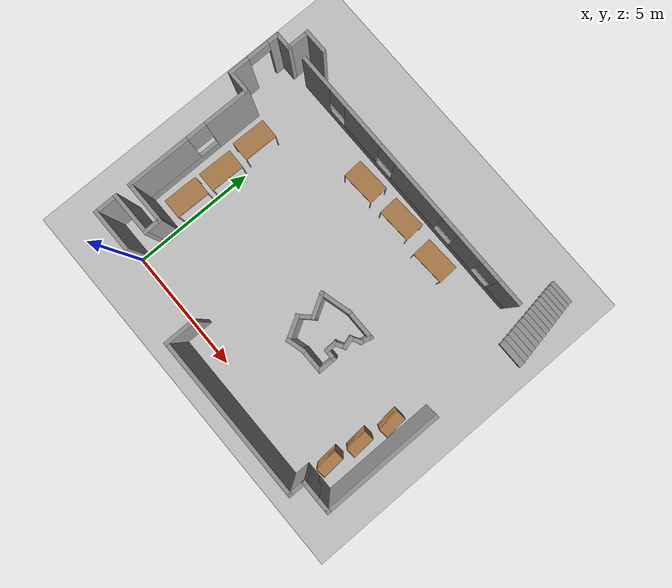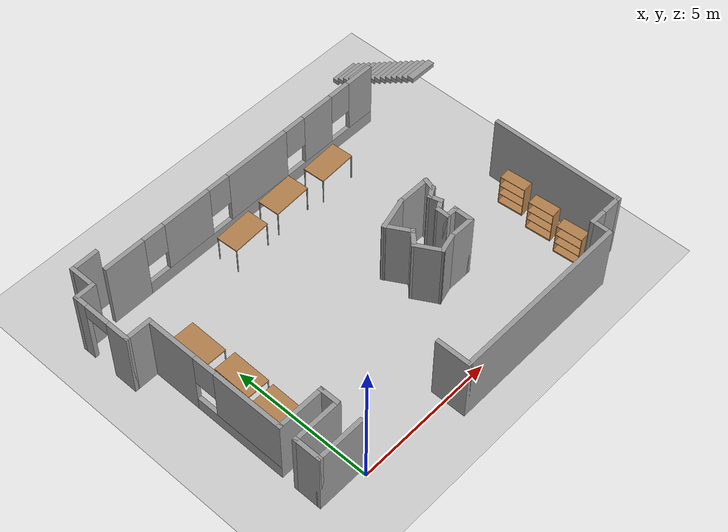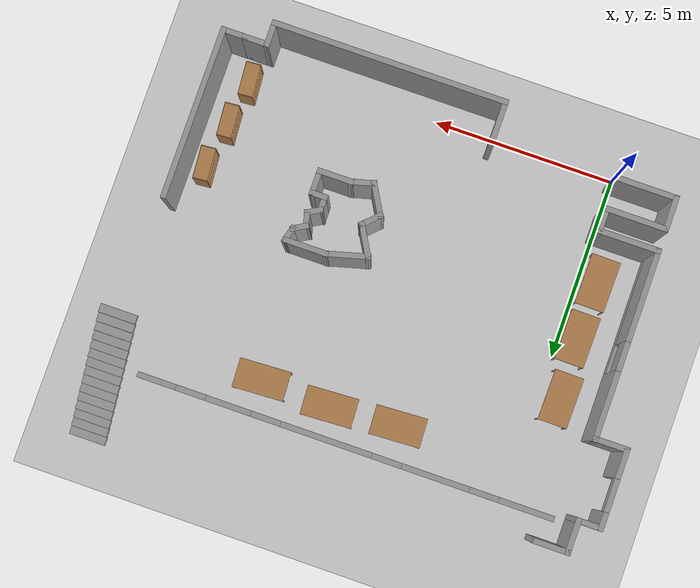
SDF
<sdf version="1.6">
 <world name="default">
  <light name="sun" type="directional">
   <pose>0 0 10 0 -0 0</pose>
   <diffuse>0.8 0.8 0.8 1</diffuse>
   <specular>0.1 0.1 0.1 1</specular>
   <attenuation>
    <range>1000</range>
    <constant>0.9</constant>
    <linear>0.01</linear>
    <quadratic>0.001</quadratic>
   </attenuation>
   <direction>-0.5 0.5 -1</direction>
  </light>
  <model name="ground_plane">
   <static>1</static>
   <link name="link">
    <collision name="collision">
     <geometry><plane><normal>0 0 1</normal><size>100 100</size></plane></geometry>
     <surface><friction><ode><mu>100</mu><mu2>50</mu2></ode></friction></surface>
    </collision>
    <visual name="visual">
     <cast_shadows>0</cast_shadows>
     <geometry><plane><normal>0 0 1</normal><size>100 100</size></plane></geometry>
     <material>
      <script><uri>file://media/materials/scripts/gazebo.material</uri><name>Gazebo/Grey</name></script>
     </material>
    </visual>
   </link>
  </model>
  <gravity>0 0 -9.8</gravity>
  <magnetic_field>6e-06 2.3e-05 -4.2e-05</magnetic_field>
  <atmosphere type="adiabatic"/>
  <physics name="default_physics" default="0" type="ode">
   <max_step_size>0.001</max_step_size>
   <real_time_factor>1</real_time_factor>
   <real_time_update_rate>1000</real_time_update_rate>
  </physics>
  <scene><ambient>0.4 0.4 0.4 1</ambient><background>0.7 0.7 0.7 1</background><shadows>1</shadows></scene>
  <spherical_coordinates>
   <surface_model>EARTH_WGS84</surface_model>
   <latitude_deg>0</latitude_deg>
   <longitude_deg>0</longitude_deg>
   <elevation>0</elevation>
   <heading_deg>0</heading_deg>
  </spherical_coordinates>
  <model name="table">
   <static>0</static>
   <link name="link">
    <collision name="surface">
     <pose>0 0 1 0 -0 0</pose>
     <geometry><box><size>1.5 0.8 0.03</size></box></geometry>
     <surface><friction><ode><mu>0.6</mu><mu2>0.6</mu2></ode></friction></surface>
    </collision>
    <visual name="visual1">
     <pose>0 0 1 0 -0 0</pose>
     <geometry><box><size>1.4 0.8 0.04</size></box></geometry>
     <material>
      <script><uri>file://media/materials/scripts/gazebo.material</uri><name>Gazebo/Wood</name></script>
     </material>
    </visual>
    <collision name="front_left_leg">
     <pose>0.68 0.38 0.5 0 -0 0</pose>
     <geometry><cylinder><radius>0.02</radius><length>1</length></cylinder></geometry>
    </collision>
    <visual name="front_left_leg">
     <pose>0.68 0.38 0.5 0 -0 0</pose>
     <geometry><cylinder><radius>0.02</radius><length>1</length></cylinder></geometry>
     <material>
      <script><uri>file://media/materials/scripts/gazebo.material</uri><name>Gazebo/Grey</name></script>
     </material>
    </visual>
    <collision name="front_right_leg">
     <pose>0.68 -0.38 0.5 0 -0 0</pose>
     <geometry><cylinder><radius>0.02</radius><length>1</length></cylinder></geometry>
    </collision>
    <visual name="front_right_leg">
     <pose>0.68 -0.38 0.5 0 -0 0</pose>
     <geometry><cylinder><radius>0.02</radius><length>1</length></cylinder></geometry>
     <material>
      <script><uri>file://media/materials/scripts/gazebo.material</uri><name>Gazebo/Grey</name></script>
     </material>
    </visual>
    <collision name="back_right_leg">
     <pose>-0.68 -0.38 0.5 0 -0 0</pose>
     <geometry><cylinder><radius>0.02</radius><length>1</length></cylinder></geometry>
    </collision>
    <visual name="back_right_leg">
     <pose>-0.68 -0.38 0.5 0 -0 0</pose>
     <geometry><cylinder><radius>0.02</radius><length>1</length></cylinder></geometry>
     <material>
      <script><uri>file://media/materials/scripts/gazebo.material</uri><name>Gazebo/Grey</name></script>
     </material>
    </visual>
    <collision name="back_left_leg">
     <pose>-0.68 0.38 0.5 0 -0 0</pose>
     <geometry><cylinder><radius>0.02</radius><length>1</length></cylinder></geometry>
    </collision>
    <visual name="back_left_leg">
     <pose>-0.68 0.38 0.5 0 -0 0</pose>
     <geometry><cylinder><radius>0.02</radius><length>1</length></cylinder></geometry>
     <material>
      <script><uri>file://media/materials/scripts/gazebo.material</uri><name>Gazebo/Grey</name></script>
     </material>
    </visual>
    <inertial>
     <inertia><ixx>1</ixx><ixy>0</ixy><ixz>0</ixz><iyy>1</iyy><iyz>0</iyz><izz>1</izz></inertia>
     <mass>1</mass>
    </inertial>
   </link>
   <pose>-0.462285 2.82795 -9e-06 0 1e-06 1.55518</pose>
  </model>
  <model name="table_clone">
   <static>0</static>
   <link name="link">
    <collision name="surface">
     <pose>0 0 1 0 -0 0</pose>
     <geometry><box><size>1.5 0.8 0.03</size></box></geometry>
     <surface><friction><ode><mu>0.6</mu><mu2>0.6</mu2></ode></friction></surface>
    </collision>
    <visual name="visual1">
     <pose>0 0 1 0 -0 0</pose>
     <geometry><box><size>1.4 0.8 0.04</size></box></geometry>
     <material>
      <script><uri>file://media/materials/scripts/gazebo.material</uri><name>Gazebo/Wood</name></script>
     </material>
    </visual>
    <collision name="front_left_leg">
     <pose>0.68 0.38 0.5 0 -0 0</pose>
     <geometry><cylinder><radius>0.02</radius><length>1</length></cylinder></geometry>
    </collision>
    <visual name="front_left_leg">
     <pose>0.68 0.38 0.5 0 -0 0</pose>
     <geometry><cylinder><radius>0.02</radius><length>1</length></cylinder></geometry>
     <material>
      <script><uri>file://media/materials/scripts/gazebo.material</uri><name>Gazebo/Grey</name></script>
     </material>
    </visual>
    <collision name="front_right_leg">
     <pose>0.68 -0.38 0.5 0 -0 0</pose>
     <geometry><cylinder><radius>0.02</radius><length>1</length></cylinder></geometry>
    </collision>
    <visual name="front_right_leg">
     <pose>0.68 -0.38 0.5 0 -0 0</pose>
     <geometry><cylinder><radius>0.02</radius><length>1</length></cylinder></geometry>
     <material>
      <script><uri>file://media/materials/scripts/gazebo.material</uri><name>Gazebo/Grey</name></script>
     </material>
    </visual>
    <collision name="back_right_leg">
     <pose>-0.68 -0.38 0.5 0 -0 0</pose>
     <geometry><cylinder><radius>0.02</radius><length>1</length></cylinder></geometry>
    </collision>
    <visual name="back_right_leg">
     <pose>-0.68 -0.38 0.5 0 -0 0</pose>
     <geometry><cylinder><radius>0.02</radius><length>1</length></cylinder></geometry>
     <material>
      <script><uri>file://media/materials/scripts/gazebo.material</uri><name>Gazebo/Grey</name></script>
     </material>
    </visual>
    <collision name="back_left_leg">
     <pose>-0.68 0.38 0.5 0 -0 0</pose>
     <geometry><cylinder><radius>0.02</radius><length>1</length></cylinder></geometry>
    </collision>
    <visual name="back_left_leg">
     <pose>-0.68 0.38 0.5 0 -0 0</pose>
     <geometry><cylinder><radius>0.02</radius><length>1</length></cylinder></geometry>
     <material>
      <script><uri>file://media/materials/scripts/gazebo.material</uri><name>Gazebo/Grey</name></script>
     </material>
    </visual>
    <inertial>
     <inertia><ixx>1</ixx><ixy>0</ixy><ixz>0</ixz><iyy>1</iyy><iyz>0</iyz><izz>1</izz></inertia>
     <mass>1</mass>
    </inertial>
   </link>
   <pose>-0.425887 4.40027 -9e-06 0 1e-06 1.55518</pose>
  </model>
  <model name="table_clone_0">
   <static>0</static>
   <link name="link">
    <collision name="surface">
     <pose>0 0 1 0 -0 0</pose>
     <geometry><box><size>1.5 0.8 0.03</size></box></geometry>
     <surface><friction><ode><mu>0.6</mu><mu2>0.6</mu2></ode></friction></surface>
    </collision>
    <visual name="visual1">
     <pose>0 0 1 0 -0 0</pose>
     <geometry><box><size>1.4 0.8 0.04</size></box></geometry>
     <material>
      <script><uri>file://media/materials/scripts/gazebo.material</uri><name>Gazebo/Wood</name></script>
     </material>
    </visual>
    <collision name="front_left_leg">
     <pose>0.68 0.38 0.5 0 -0 0</pose>
     <geometry><cylinder><radius>0.02</radius><length>1</length></cylinder></geometry>
    </collision>
    <visual name="front_left_leg">
     <pose>0.68 0.38 0.5 0 -0 0</pose>
     <geometry><cylinder><radius>0.02</radius><length>1</length></cylinder></geometry>
     <material>
      <script><uri>file://media/materials/scripts/gazebo.material</uri><name>Gazebo/Grey</name></script>
     </material>
    </visual>
    <collision name="front_right_leg">
     <pose>0.68 -0.38 0.5 0 -0 0</pose>
     <geometry><cylinder><radius>0.02</radius><length>1</length></cylinder></geometry>
    </collision>
    <visual name="front_right_leg">
     <pose>0.68 -0.38 0.5 0 -0 0</pose>
     <geometry><cylinder><radius>0.02</radius><length>1</length></cylinder></geometry>
     <material>
      <script><uri>file://media/materials/scripts/gazebo.material</uri><name>Gazebo/Grey</name></script>
     </material>
    </visual>
    <collision name="back_right_leg">
     <pose>-0.68 -0.38 0.5 0 -0 0</pose>
     <geometry><cylinder><radius>0.02</radius><length>1</length></cylinder></geometry>
    </collision>
    <visual name="back_right_leg">
     <pose>-0.68 -0.38 0.5 0 -0 0</pose>
     <geometry><cylinder><radius>0.02</radius><length>1</length></cylinder></geometry>
     <material>
      <script><uri>file://media/materials/scripts/gazebo.material</uri><name>Gazebo/Grey</name></script>
     </material>
    </visual>
    <collision name="back_left_leg">
     <pose>-0.68 0.38 0.5 0 -0 0</pose>
     <geometry><cylinder><radius>0.02</radius><length>1</length></cylinder></geometry>
    </collision>
    <visual name="back_left_leg">
     <pose>-0.68 0.38 0.5 0 -0 0</pose>
     <geometry><cylinder><radius>0.02</radius><length>1</length></cylinder></geometry>
     <material>
      <script><uri>file://media/materials/scripts/gazebo.material</uri><name>Gazebo/Grey</name></script>
     </material>
    </visual>
    <inertial>
     <inertia><ixx>1</ixx><ixy>0</ixy><ixz>0</ixz><iyy>1</iyy><iyz>0</iyz><izz>1</izz></inertia>
     <mass>1</mass>
    </inertial>
   </link>
   <pose>-0.519405 6.05381 -9e-06 0 1e-06 1.55518</pose>
  </model>
  <model name="pared_lab">
   <pose>4.41876 9.09094 0 0 -0 0</pose>
   <link name="Wall_5">
    <visual name="Wall_5_Visual_0">
     <pose>-4.88226 0 1.25 0 -0 0</pose>
     <geometry><box><size>1.48549 0.15 2.5</size></box></geometry>
     <material>
      <script><uri>file://media/materials/scripts/gazebo.material</uri><name>Gazebo/Grey</name></script>
      <ambient>1 1 1 1</ambient>
     </material>
    </visual>
    <collision name="Wall_5_Collision_0">
     <geometry><box><size>1.48549 0.15 2.5</size></box></geometry>
     <pose>-4.88226 0 1.25 0 -0 0</pose>
    </collision>
    <visual name="Wall_5_Visual_1">
     <pose>0.742744 0 0.25 0 -0 0</pose>
     <geometry><box><size>9.76451 0.15 0.5</size></box></geometry>
     <material>
      <script><uri>file://media/materials/scripts/gazebo.material</uri><name>Gazebo/Grey</name></script>
      <ambient>1 1 1 1</ambient>
     </material>
    </visual>
    <collision name="Wall_5_Collision_1">
     <geometry><box><size>9.76451 0.15 0.5</size></box></geometry>
     <pose>0.742744 0 0.25 0 -0 0</pose>
    </collision>
    <visual name="Wall_5_Visual_2">
     <pose>-2.4287 0 1.5 0 -0 0</pose>
     <geometry><box><size>1.82162 0.15 2</size></box></geometry>
     <material>
      <script><uri>file://media/materials/scripts/gazebo.material</uri><name>Gazebo/Grey</name></script>
      <ambient>1 1 1 1</ambient>
     </material>
    </visual>
    <collision name="Wall_5_Collision_2">
     <geometry><box><size>1.82162 0.15 2</size></box></geometry>
     <pose>-2.4287 0 1.5 0 -0 0</pose>
    </collision>
    <visual name="Wall_5_Visual_3">
     <pose>0.513937 0 1.5 0 -0 0</pose>
     <geometry><box><size>2.46365 0.15 2</size></box></geometry>
     <material>
      <script><uri>file://media/materials/scripts/gazebo.material</uri><name>Gazebo/Grey</name></script>
      <ambient>1 1 1 1</ambient>
     </material>
    </visual>
    <collision name="Wall_5_Collision_3">
     <geometry><box><size>2.46365 0.15 2</size></box></geometry>
     <pose>0.513937 0 1.5 0 -0 0</pose>
    </collision>
    <visual name="Wall_5_Visual_4">
     <pose>3.16231 0 1.5 0 -0 0</pose>
     <geometry><box><size>1.2331 0.15 2</size></box></geometry>
     <material>
      <script><uri>file://media/materials/scripts/gazebo.material</uri><name>Gazebo/Grey</name></script>
      <ambient>1 1 1 1</ambient>
     </material>
    </visual>
    <collision name="Wall_5_Collision_4">
     <geometry><box><size>1.2331 0.15 2</size></box></geometry>
     <pose>3.16231 0 1.5 0 -0 0</pose>
    </collision>
    <visual name="Wall_5_Visual_5">
     <pose>5.10193 0 1.5 0 -0 0</pose>
     <geometry><box><size>1.04614 0.15 2</size></box></geometry>
     <material>
      <script><uri>file://media/materials/scripts/gazebo.material</uri><name>Gazebo/Grey</name></script>
      <ambient>1 1 1 1</ambient>
     </material>
    </visual>
    <collision name="Wall_5_Collision_5">
     <geometry><box><size>1.04614 0.15 2</size></box></geometry>
     <pose>5.10193 0 1.5 0 -0 0</pose>
    </collision>
    <visual name="Wall_5_Visual_6">
     <pose>-3.73951 0 1.9 0 -0 0</pose>
     <geometry><box><size>0.8 0.15 1.2</size></box></geometry>
     <material>
      <script><uri>file://media/materials/scripts/gazebo.material</uri><name>Gazebo/Grey</name></script>
      <ambient>1 1 1 1</ambient>
     </material>
    </visual>
    <collision name="Wall_5_Collision_6">
     <geometry><box><size>0.8 0.15 1.2</size></box></geometry>
     <pose>-3.73951 0 1.9 0 -0 0</pose>
    </collision>
    <visual name="Wall_5_Visual_7">
     <pose>-1.11789 0 1.9 0 -0 0</pose>
     <geometry><box><size>0.8 0.15 1.2</size></box></geometry>
     <material>
      <script><uri>file://media/materials/scripts/gazebo.material</uri><name>Gazebo/Grey</name></script>
      <ambient>1 1 1 1</ambient>
     </material>
    </visual>
    <collision name="Wall_5_Collision_7">
     <geometry><box><size>0.8 0.15 1.2</size></box></geometry>
     <pose>-1.11789 0 1.9 0 -0 0</pose>
    </collision>
    <visual name="Wall_5_Visual_8">
     <pose>2.14576 0 1.9 0 -0 0</pose>
     <geometry><box><size>0.8 0.15 1.2</size></box></geometry>
     <material>
      <script><uri>file://media/materials/scripts/gazebo.material</uri><name>Gazebo/Grey</name></script>
      <ambient>1 1 1 1</ambient>
     </material>
    </visual>
    <collision name="Wall_5_Collision_8">
     <geometry><box><size>0.8 0.15 1.2</size></box></geometry>
     <pose>2.14576 0 1.9 0 -0 0</pose>
    </collision>
    <visual name="Wall_5_Visual_9">
     <pose>4.17886 0 1.9 0 -0 0</pose>
     <geometry><box><size>0.8 0.15 1.2</size></box></geometry>
     <material>
      <script><uri>file://media/materials/scripts/gazebo.material</uri><name>Gazebo/Grey</name></script>
      <ambient>1 1 1 1</ambient>
     </material>
    </visual>
    <collision name="Wall_5_Collision_9">
     <geometry><box><size>0.8 0.15 1.2</size></box></geometry>
     <pose>4.17886 0 1.9 0 -0 0</pose>
    </collision>
   </link>
   <static>1</static>
  </model>
  <model name="table_clone_1">
   <static>0</static>
   <link name="link">
    <collision name="surface">
     <pose>0 0 1 0 -0 0</pose>
     <geometry><box><size>1.5 0.8 0.03</size></box></geometry>
     <surface><friction><ode><mu>0.6</mu><mu2>0.6</mu2></ode></friction></surface>
    </collision>
    <visual name="visual1">
     <pose>0 0 1 0 -0 0</pose>
     <geometry><box><size>1.4 0.8 0.04</size></box></geometry>
     <material>
      <script><uri>file://media/materials/scripts/gazebo.material</uri><name>Gazebo/Wood</name></script>
     </material>
    </visual>
    <collision name="front_left_leg">
     <pose>0.68 0.38 0.5 0 -0 0</pose>
     <geometry><cylinder><radius>0.02</radius><length>1</length></cylinder></geometry>
    </collision>
    <visual name="front_left_leg">
     <pose>0.68 0.38 0.5 0 -0 0</pose>
     <geometry><cylinder><radius>0.02</radius><length>1</length></cylinder></geometry>
     <material>
      <script><uri>file://media/materials/scripts/gazebo.material</uri><name>Gazebo/Grey</name></script>
     </material>
    </visual>
    <collision name="front_right_leg">
     <pose>0.68 -0.38 0.5 0 -0 0</pose>
     <geometry><cylinder><radius>0.02</radius><length>1</length></cylinder></geometry>
    </collision>
    <visual name="front_right_leg">
     <pose>0.68 -0.38 0.5 0 -0 0</pose>
     <geometry><cylinder><radius>0.02</radius><length>1</length></cylinder></geometry>
     <material>
      <script><uri>file://media/materials/scripts/gazebo.material</uri><name>Gazebo/Grey</name></script>
     </material>
    </visual>
    <collision name="back_right_leg">
     <pose>-0.68 -0.38 0.5 0 -0 0</pose>
     <geometry><cylinder><radius>0.02</radius><length>1</length></cylinder></geometry>
    </collision>
    <visual name="back_right_leg">
     <pose>-0.68 -0.38 0.5 0 -0 0</pose>
     <geometry><cylinder><radius>0.02</radius><length>1</length></cylinder></geometry>
     <material>
      <script><uri>file://media/materials/scripts/gazebo.material</uri><name>Gazebo/Grey</name></script>
     </material>
    </visual>
    <collision name="back_left_leg">
     <pose>-0.68 0.38 0.5 0 -0 0</pose>
     <geometry><cylinder><radius>0.02</radius><length>1</length></cylinder></geometry>
    </collision>
    <visual name="back_left_leg">
     <pose>-0.68 0.38 0.5 0 -0 0</pose>
     <geometry><cylinder><radius>0.02</radius><length>1</length></cylinder></geometry>
     <material>
      <script><uri>file://media/materials/scripts/gazebo.material</uri><name>Gazebo/Grey</name></script>
     </material>
    </visual>
    <inertial>
     <inertia><ixx>1</ixx><ixy>0</ixy><ixz>0</ixz><iyy>1</iyy><iyz>0</iyz><izz>1</izz></inertia>
     <mass>1</mass>
    </inertial>
   </link>
   <pose>3.2962 8.13733 -1e-06 0 1e-06 0.048714</pose>
  </model>
  <model name="table_clone_1_clone">
   <static>0</static>
   <link name="link">
    <collision name="surface">
     <pose>0 0 1 0 -0 0</pose>
     <geometry><box><size>1.5 0.8 0.03</size></box></geometry>
     <surface><friction><ode><mu>0.6</mu><mu2>0.6</mu2></ode></friction></surface>
    </collision>
    <visual name="visual1">
     <pose>0 0 1 0 -0 0</pose>
     <geometry><box><size>1.4 0.8 0.04</size></box></geometry>
     <material>
      <script><uri>file://media/materials/scripts/gazebo.material</uri><name>Gazebo/Wood</name></script>
     </material>
    </visual>
    <collision name="front_left_leg">
     <pose>0.68 0.38 0.5 0 -0 0</pose>
     <geometry><cylinder><radius>0.02</radius><length>1</length></cylinder></geometry>
    </collision>
    <visual name="front_left_leg">
     <pose>0.68 0.38 0.5 0 -0 0</pose>
     <geometry><cylinder><radius>0.02</radius><length>1</length></cylinder></geometry>
     <material>
      <script><uri>file://media/materials/scripts/gazebo.material</uri><name>Gazebo/Grey</name></script>
     </material>
    </visual>
    <collision name="front_right_leg">
     <pose>0.68 -0.38 0.5 0 -0 0</pose>
     <geometry><cylinder><radius>0.02</radius><length>1</length></cylinder></geometry>
    </collision>
    <visual name="front_right_leg">
     <pose>0.68 -0.38 0.5 0 -0 0</pose>
     <geometry><cylinder><radius>0.02</radius><length>1</length></cylinder></geometry>
     <material>
      <script><uri>file://media/materials/scripts/gazebo.material</uri><name>Gazebo/Grey</name></script>
     </material>
    </visual>
    <collision name="back_right_leg">
     <pose>-0.68 -0.38 0.5 0 -0 0</pose>
     <geometry><cylinder><radius>0.02</radius><length>1</length></cylinder></geometry>
    </collision>
    <visual name="back_right_leg">
     <pose>-0.68 -0.38 0.5 0 -0 0</pose>
     <geometry><cylinder><radius>0.02</radius><length>1</length></cylinder></geometry>
     <material>
      <script><uri>file://media/materials/scripts/gazebo.material</uri><name>Gazebo/Grey</name></script>
     </material>
    </visual>
    <collision name="back_left_leg">
     <pose>-0.68 0.38 0.5 0 -0 0</pose>
     <geometry><cylinder><radius>0.02</radius><length>1</length></cylinder></geometry>
    </collision>
    <visual name="back_left_leg">
     <pose>-0.68 0.38 0.5 0 -0 0</pose>
     <geometry><cylinder><radius>0.02</radius><length>1</length></cylinder></geometry>
     <material>
      <script><uri>file://media/materials/scripts/gazebo.material</uri><name>Gazebo/Grey</name></script>
     </material>
    </visual>
    <inertial>
     <inertia><ixx>1</ixx><ixy>0</ixy><ixz>0</ixz><iyy>1</iyy><iyz>0</iyz><izz>1</izz></inertia>
     <mass>1</mass>
    </inertial>
   </link>
   <pose>5.17274 8.24378 -1e-05 0 -0 0.048714</pose>
  </model>
  <model name="table_clone_1_clone_0">
   <static>0</static>
   <link name="link">
    <collision name="surface">
     <pose>0 0 1 0 -0 0</pose>
     <geometry><box><size>1.5 0.8 0.03</size></box></geometry>
     <surface><friction><ode><mu>0.6</mu><mu2>0.6</mu2></ode></friction></surface>
    </collision>
    <visual name="visual1">
     <pose>0 0 1 0 -0 0</pose>
     <geometry><box><size>1.4 0.8 0.04</size></box></geometry>
     <material>
      <script><uri>file://media/materials/scripts/gazebo.material</uri><name>Gazebo/Wood</name></script>
     </material>
    </visual>
    <collision name="front_left_leg">
     <pose>0.68 0.38 0.5 0 -0 0</pose>
     <geometry><cylinder><radius>0.02</radius><length>1</length></cylinder></geometry>
    </collision>
    <visual name="front_left_leg">
     <pose>0.68 0.38 0.5 0 -0 0</pose>
     <geometry><cylinder><radius>0.02</radius><length>1</length></cylinder></geometry>
     <material>
      <script><uri>file://media/materials/scripts/gazebo.material</uri><name>Gazebo/Grey</name></script>
     </material>
    </visual>
    <collision name="front_right_leg">
     <pose>0.68 -0.38 0.5 0 -0 0</pose>
     <geometry><cylinder><radius>0.02</radius><length>1</length></cylinder></geometry>
    </collision>
    <visual name="front_right_leg">
     <pose>0.68 -0.38 0.5 0 -0 0</pose>
     <geometry><cylinder><radius>0.02</radius><length>1</length></cylinder></geometry>
     <material>
      <script><uri>file://media/materials/scripts/gazebo.material</uri><name>Gazebo/Grey</name></script>
     </material>
    </visual>
    <collision name="back_right_leg">
     <pose>-0.68 -0.38 0.5 0 -0 0</pose>
     <geometry><cylinder><radius>0.02</radius><length>1</length></cylinder></geometry>
    </collision>
    <visual name="back_right_leg">
     <pose>-0.68 -0.38 0.5 0 -0 0</pose>
     <geometry><cylinder><radius>0.02</radius><length>1</length></cylinder></geometry>
     <material>
      <script><uri>file://media/materials/scripts/gazebo.material</uri><name>Gazebo/Grey</name></script>
     </material>
    </visual>
    <collision name="back_left_leg">
     <pose>-0.68 0.38 0.5 0 -0 0</pose>
     <geometry><cylinder><radius>0.02</radius><length>1</length></cylinder></geometry>
    </collision>
    <visual name="back_left_leg">
     <pose>-0.68 0.38 0.5 0 -0 0</pose>
     <geometry><cylinder><radius>0.02</radius><length>1</length></cylinder></geometry>
     <material>
      <script><uri>file://media/materials/scripts/gazebo.material</uri><name>Gazebo/Grey</name></script>
     </material>
    </visual>
    <inertial>
     <inertia><ixx>1</ixx><ixy>0</ixy><ixz>0</ixz><iyy>1</iyy><iyz>0</iyz><izz>1</izz></inertia>
     <mass>1</mass>
    </inertial>
   </link>
   <pose>7.09873 8.15476 -1e-06 0 1e-06 0.048714</pose>
  </model>
  <model name="bookshelf">
   <static>1</static>
   <link name="link">
    <inertial><mass>1</mass></inertial>
    <collision name="back">
     <pose>0 0.005 0.6 0 -0 0</pose>
     <geometry><box><size>0.9 0.01 1.2</size></box></geometry>
    </collision>
    <visual name="visual1">
     <pose>0 0.005 0.6 0 -0 0</pose>
     <geometry><box><size>0.9 0.01 1.2</size></box></geometry>
     <material>
      <script><uri>file://media/materials/scripts/gazebo.material</uri><name>Gazebo/Wood</name></script>
     </material>
    </visual>
    <collision name="left_side">
     <pose>0.45 -0.195 0.6 0 -0 0</pose>
     <geometry><box><size>0.02 0.4 1.2</size></box></geometry>
    </collision>
    <visual name="visual2">
     <pose>0.45 -0.195 0.6 0 -0 0</pose>
     <geometry><box><size>0.02 0.4 1.2</size></box></geometry>
     <material>
      <script><uri>file://media/materials/scripts/gazebo.material</uri><name>Gazebo/Wood</name></script>
     </material>
    </visual>
    <collision name="right_side">
     <pose>-0.45 -0.195 0.6 0 -0 0</pose>
     <geometry><box><size>0.02 0.4 1.2</size></box></geometry>
    </collision>
    <visual name="visual3">
     <pose>-0.45 -0.195 0.6 0 -0 0</pose>
     <geometry><box><size>0.02 0.4 1.2</size></box></geometry>
     <material>
      <script><uri>file://media/materials/scripts/gazebo.material</uri><name>Gazebo/Wood</name></script>
     </material>
    </visual>
    <collision name="bottom">
     <pose>0 -0.195 0.03 0 -0 0</pose>
     <geometry><box><size>0.88 0.4 0.06</size></box></geometry>
    </collision>
    <visual name="visual4">
     <pose>0 -0.195 0.03 0 -0 0</pose>
     <geometry><box><size>0.88 0.4 0.06</size></box></geometry>
     <material>
      <script><uri>file://media/materials/scripts/gazebo.material</uri><name>Gazebo/Wood</name></script>
     </material>
    </visual>
    <collision name="top">
     <pose>0 -0.195 1.19 0 -0 0</pose>
     <geometry><box><size>0.88 0.4 0.02</size></box></geometry>
    </collision>
    <visual name="visual5">
     <pose>0 -0.195 1.19 0 -0 0</pose>
     <geometry><box><size>0.88 0.4 0.02</size></box></geometry>
     <material>
      <script><uri>file://media/materials/scripts/gazebo.material</uri><name>Gazebo/Wood</name></script>
     </material>
    </visual>
    <collision name="low_shelf">
     <pose>0 -0.195 0.43 0 -0 0</pose>
     <geometry><box><size>0.88 0.4 0.02</size></box></geometry>
    </collision>
    <visual name="visual6">
     <pose>0 -0.195 0.43 0 -0 0</pose>
     <geometry><box><size>0.88 0.4 0.02</size></box></geometry>
     <material>
      <script><uri>file://media/materials/scripts/gazebo.material</uri><name>Gazebo/Wood</name></script>
     </material>
    </visual>
    <collision name="high_shelf">
     <pose>0 -0.195 0.8 0 -0 0</pose>
     <geometry><box><size>0.88 0.4 0.02</size></box></geometry>
    </collision>
    <visual name="visual7">
     <pose>0 -0.195 0.8 0 -0 0</pose>
     <geometry><box><size>0.88 0.4 0.02</size></box></geometry>
     <material>
      <script><uri>file://media/materials/scripts/gazebo.material</uri><name>Gazebo/Wood</name></script>
     </material>
    </visual>
   </link>
   <pose>10.6229 3.26593 0 0 0 -1.49467</pose>
  </model>
  <model name="bookshelf_clone">
   <static>1</static>
   <link name="link">
    <inertial><mass>1</mass></inertial>
    <collision name="back">
     <pose>0 0.005 0.6 0 -0 0</pose>
     <geometry><box><size>0.9 0.01 1.2</size></box></geometry>
    </collision>
    <visual name="visual1">
     <pose>0 0.005 0.6 0 -0 0</pose>
     <geometry><box><size>0.9 0.01 1.2</size></box></geometry>
     <material>
      <script><uri>file://media/materials/scripts/gazebo.material</uri><name>Gazebo/Wood</name></script>
     </material>
    </visual>
    <collision name="left_side">
     <pose>0.45 -0.195 0.6 0 -0 0</pose>
     <geometry><box><size>0.02 0.4 1.2</size></box></geometry>
    </collision>
    <visual name="visual2">
     <pose>0.45 -0.195 0.6 0 -0 0</pose>
     <geometry><box><size>0.02 0.4 1.2</size></box></geometry>
     <material>
      <script><uri>file://media/materials/scripts/gazebo.material</uri><name>Gazebo/Wood</name></script>
     </material>
    </visual>
    <collision name="right_side">
     <pose>-0.45 -0.195 0.6 0 -0 0</pose>
     <geometry><box><size>0.02 0.4 1.2</size></box></geometry>
    </collision>
    <visual name="visual3">
     <pose>-0.45 -0.195 0.6 0 -0 0</pose>
     <geometry><box><size>0.02 0.4 1.2</size></box></geometry>
     <material>
      <script><uri>file://media/materials/scripts/gazebo.material</uri><name>Gazebo/Wood</name></script>
     </material>
    </visual>
    <collision name="bottom">
     <pose>0 -0.195 0.03 0 -0 0</pose>
     <geometry><box><size>0.88 0.4 0.06</size></box></geometry>
    </collision>
    <visual name="visual4">
     <pose>0 -0.195 0.03 0 -0 0</pose>
     <geometry><box><size>0.88 0.4 0.06</size></box></geometry>
     <material>
      <script><uri>file://media/materials/scripts/gazebo.material</uri><name>Gazebo/Wood</name></script>
     </material>
    </visual>
    <collision name="top">
     <pose>0 -0.195 1.19 0 -0 0</pose>
     <geometry><box><size>0.88 0.4 0.02</size></box></geometry>
    </collision>
    <visual name="visual5">
     <pose>0 -0.195 1.19 0 -0 0</pose>
     <geometry><box><size>0.88 0.4 0.02</size></box></geometry>
     <material>
      <script><uri>file://media/materials/scripts/gazebo.material</uri><name>Gazebo/Wood</name></script>
     </material>
    </visual>
    <collision name="low_shelf">
     <pose>0 -0.195 0.43 0 -0 0</pose>
     <geometry><box><size>0.88 0.4 0.02</size></box></geometry>
    </collision>
    <visual name="visual6">
     <pose>0 -0.195 0.43 0 -0 0</pose>
     <geometry><box><size>0.88 0.4 0.02</size></box></geometry>
     <material>
      <script><uri>file://media/materials/scripts/gazebo.material</uri><name>Gazebo/Wood</name></script>
     </material>
    </visual>
    <collision name="high_shelf">
     <pose>0 -0.195 0.8 0 -0 0</pose>
     <geometry><box><size>0.88 0.4 0.02</size></box></geometry>
    </collision>
    <visual name="visual7">
     <pose>0 -0.195 0.8 0 -0 0</pose>
     <geometry><box><size>0.88 0.4 0.02</size></box></geometry>
     <material>
      <script><uri>file://media/materials/scripts/gazebo.material</uri><name>Gazebo/Wood</name></script>
     </material>
    </visual>
   </link>
   <pose>10.4114 1.97434 0 0 0 -1.49467</pose>
  </model>
  <model name="bookshelf_clone_0">
   <static>1</static>
   <link name="link">
    <inertial><mass>1</mass></inertial>
    <collision name="back">
     <pose>0 0.005 0.6 0 -0 0</pose>
     <geometry><box><size>0.9 0.01 1.2</size></box></geometry>
    </collision>
    <visual name="visual1">
     <pose>0 0.005 0.6 0 -0 0</pose>
     <geometry><box><size>0.9 0.01 1.2</size></box></geometry>
     <material>
      <script><uri>file://media/materials/scripts/gazebo.material</uri><name>Gazebo/Wood</name></script>
     </material>
    </visual>
    <collision name="left_side">
     <pose>0.45 -0.195 0.6 0 -0 0</pose>
     <geometry><box><size>0.02 0.4 1.2</size></box></geometry>
    </collision>
    <visual name="visual2">
     <pose>0.45 -0.195 0.6 0 -0 0</pose>
     <geometry><box><size>0.02 0.4 1.2</size></box></geometry>
     <material>
      <script><uri>file://media/materials/scripts/gazebo.material</uri><name>Gazebo/Wood</name></script>
     </material>
    </visual>
    <collision name="right_side">
     <pose>-0.45 -0.195 0.6 0 -0 0</pose>
     <geometry><box><size>0.02 0.4 1.2</size></box></geometry>
    </collision>
    <visual name="visual3">
     <pose>-0.45 -0.195 0.6 0 -0 0</pose>
     <geometry><box><size>0.02 0.4 1.2</size></box></geometry>
     <material>
      <script><uri>file://media/materials/scripts/gazebo.material</uri><name>Gazebo/Wood</name></script>
     </material>
    </visual>
    <collision name="bottom">
     <pose>0 -0.195 0.03 0 -0 0</pose>
     <geometry><box><size>0.88 0.4 0.06</size></box></geometry>
    </collision>
    <visual name="visual4">
     <pose>0 -0.195 0.03 0 -0 0</pose>
     <geometry><box><size>0.88 0.4 0.06</size></box></geometry>
     <material>
      <script><uri>file://media/materials/scripts/gazebo.material</uri><name>Gazebo/Wood</name></script>
     </material>
    </visual>
    <collision name="top">
     <pose>0 -0.195 1.19 0 -0 0</pose>
     <geometry><box><size>0.88 0.4 0.02</size></box></geometry>
    </collision>
    <visual name="visual5">
     <pose>0 -0.195 1.19 0 -0 0</pose>
     <geometry><box><size>0.88 0.4 0.02</size></box></geometry>
     <material>
      <script><uri>file://media/materials/scripts/gazebo.material</uri><name>Gazebo/Wood</name></script>
     </material>
    </visual>
    <collision name="low_shelf">
     <pose>0 -0.195 0.43 0 -0 0</pose>
     <geometry><box><size>0.88 0.4 0.02</size></box></geometry>
    </collision>
    <visual name="visual6">
     <pose>0 -0.195 0.43 0 -0 0</pose>
     <geometry><box><size>0.88 0.4 0.02</size></box></geometry>
     <material>
      <script><uri>file://media/materials/scripts/gazebo.material</uri><name>Gazebo/Wood</name></script>
     </material>
    </visual>
    <collision name="high_shelf">
     <pose>0 -0.195 0.8 0 -0 0</pose>
     <geometry><box><size>0.88 0.4 0.02</size></box></geometry>
    </collision>
    <visual name="visual7">
     <pose>0 -0.195 0.8 0 -0 0</pose>
     <geometry><box><size>0.88 0.4 0.02</size></box></geometry>
     <material>
      <script><uri>file://media/materials/scripts/gazebo.material</uri><name>Gazebo/Wood</name></script>
     </material>
    </visual>
   </link>
   <pose>10.2428 0.749843 0 0 0 -1.49467</pose>
  </model>
  <model name="paredes_simplepilab_0">
   <link name="Stairs_0">
    <visual name="Stairs_0_Visual_0">
     <pose>6.50578 5.54062 0.083333 0 -0 0</pose>
     <geometry><box><size>1 0.233333 0.166667</size></box></geometry>
     <material>
      <script><uri>file://media/materials/scripts/gazebo.material</uri><name>Gazebo/Grey</name></script>
      <ambient>1 1 1 1</ambient>
      <diffuse>0.7 0.7 0.7 1</diffuse>
      <specular>0.01 0.01 0.01 1</specular>
      <emissive>0 0 0 1</emissive>
     </material>
    </visual>
    <visual name="Stairs_0_Visual_1">
     <pose>6.50578 5.30728 0.25 0 -0 0</pose>
     <geometry><box><size>1 0.233333 0.166667</size></box></geometry>
     <material>
      <script><uri>file://media/materials/scripts/gazebo.material</uri><name>Gazebo/Grey</name></script>
      <ambient>1 1 1 1</ambient>
      <diffuse>0.7 0.7 0.7 1</diffuse>
      <specular>0.01 0.01 0.01 1</specular>
      <emissive>0 0 0 1</emissive>
     </material>
    </visual>
    <visual name="Stairs_0_Visual_2">
     <pose>6.50578 5.07395 0.416667 0 -0 0</pose>
     <geometry><box><size>1 0.233333 0.166667</size></box></geometry>
     <material>
      <script><uri>file://media/materials/scripts/gazebo.material</uri><name>Gazebo/Grey</name></script>
      <ambient>1 1 1 1</ambient>
      <diffuse>0.7 0.7 0.7 1</diffuse>
      <specular>0.01 0.01 0.01 1</specular>
      <emissive>0 0 0 1</emissive>
     </material>
    </visual>
    <visual name="Stairs_0_Visual_3">
     <pose>6.50578 4.84062 0.583333 0 -0 0</pose>
     <geometry><box><size>1 0.233333 0.166667</size></box></geometry>
     <material>
      <script><uri>file://media/materials/scripts/gazebo.material</uri><name>Gazebo/Grey</name></script>
      <ambient>1 1 1 1</ambient>
      <diffuse>0.7 0.7 0.7 1</diffuse>
      <specular>0.01 0.01 0.01 1</specular>
      <emissive>0 0 0 1</emissive>
     </material>
    </visual>
    <visual name="Stairs_0_Visual_4">
     <pose>6.50578 4.60728 0.75 0 -0 0</pose>
     <geometry><box><size>1 0.233333 0.166667</size></box></geometry>
     <material>
      <script><uri>file://media/materials/scripts/gazebo.material</uri><name>Gazebo/Grey</name></script>
      <ambient>1 1 1 1</ambient>
      <diffuse>0.7 0.7 0.7 1</diffuse>
      <specular>0.01 0.01 0.01 1</specular>
      <emissive>0 0 0 1</emissive>
     </material>
    </visual>
    <visual name="Stairs_0_Visual_5">
     <pose>6.50578 4.37395 0.916667 0 -0 0</pose>
     <geometry><box><size>1 0.233333 0.166667</size></box></geometry>
     <material>
      <script><uri>file://media/materials/scripts/gazebo.material</uri><name>Gazebo/Grey</name></script>
      <ambient>1 1 1 1</ambient>
      <diffuse>0.7 0.7 0.7 1</diffuse>
      <specular>0.01 0.01 0.01 1</specular>
      <emissive>0 0 0 1</emissive>
     </material>
    </visual>
    <visual name="Stairs_0_Visual_6">
     <pose>6.50578 4.14062 1.08333 0 -0 0</pose>
     <geometry><box><size>1 0.233333 0.166667</size></box></geometry>
     <material>
      <script><uri>file://media/materials/scripts/gazebo.material</uri><name>Gazebo/Grey</name></script>
      <ambient>1 1 1 1</ambient>
      <diffuse>0.7 0.7 0.7 1</diffuse>
      <specular>0.01 0.01 0.01 1</specular>
      <emissive>0 0 0 1</emissive>
     </material>
    </visual>
    <visual name="Stairs_0_Visual_7">
     <pose>6.50578 3.90728 1.25 0 -0 0</pose>
     <geometry><box><size>1 0.233333 0.166667</size></box></geometry>
     <material>
      <script><uri>file://media/materials/scripts/gazebo.material</uri><name>Gazebo/Grey</name></script>
      <ambient>1 1 1 1</ambient>
      <diffuse>0.7 0.7 0.7 1</diffuse>
      <specular>0.01 0.01 0.01 1</specular>
      <emissive>0 0 0 1</emissive>
     </material>
    </visual>
    <visual name="Stairs_0_Visual_8">
     <pose>6.50578 3.67395 1.41667 0 -0 0</pose>
     <geometry><box><size>1 0.233333 0.166667</size></box></geometry>
     <material>
      <script><uri>file://media/materials/scripts/gazebo.material</uri><name>Gazebo/Grey</name></script>
      <ambient>1 1 1 1</ambient>
      <diffuse>0.7 0.7 0.7 1</diffuse>
      <specular>0.01 0.01 0.01 1</specular>
      <emissive>0 0 0 1</emissive>
     </material>
    </visual>
    <visual name="Stairs_0_Visual_10">
     <pose>6.50578 3.20729 1.75 0 -0 0</pose>
     <geometry><box><size>1 0.233333 0.166667</size></box></geometry>
     <material>
      <script><uri>file://media/materials/scripts/gazebo.material</uri><name>Gazebo/Grey</name></script>
      <ambient>1 1 1 1</ambient>
      <diffuse>0.7 0.7 0.7 1</diffuse>
      <specular>0.01 0.01 0.01 1</specular>
      <emissive>0 0 0 1</emissive>
     </material>
    </visual>
    <visual name="Stairs_0_Visual_9">
     <pose>6.50578 3.44062 1.58333 0 -0 0</pose>
     <geometry><box><size>1 0.233333 0.166667</size></box></geometry>
     <material>
      <script><uri>file://media/materials/scripts/gazebo.material</uri><name>Gazebo/Grey</name></script>
      <ambient>1 1 1 1</ambient>
      <diffuse>0.7 0.7 0.7 1</diffuse>
      <specular>0.01 0.01 0.01 1</specular>
      <emissive>0 0 0 1</emissive>
     </material>
    </visual>
    <visual name="Stairs_0_Visual_11">
     <pose>6.50578 2.97395 1.91667 0 -0 0</pose>
     <geometry><box><size>1 0.233333 0.166667</size></box></geometry>
     <material>
      <script><uri>file://media/materials/scripts/gazebo.material</uri><name>Gazebo/Grey</name></script>
      <ambient>1 1 1 1</ambient>
      <diffuse>0.7 0.7 0.7 1</diffuse>
      <specular>0.01 0.01 0.01 1</specular>
      <emissive>0 0 0 1</emissive>
     </material>
    </visual>
    <visual name="Stairs_0_Visual_12">
     <pose>6.50578 2.74062 2.08333 0 -0 0</pose>
     <geometry><box><size>1 0.233333 0.166667</size></box></geometry>
     <material>
      <script><uri>file://media/materials/scripts/gazebo.material</uri><name>Gazebo/Grey</name></script>
      <ambient>1 1 1 1</ambient>
      <diffuse>0.7 0.7 0.7 1</diffuse>
      <specular>0.01 0.01 0.01 1</specular>
      <emissive>0 0 0 1</emissive>
     </material>
    </visual>
    <visual name="Stairs_0_Visual_13">
     <pose>6.50578 2.50728 2.25 0 -0 0</pose>
     <geometry><box><size>1 0.233333 0.166667</size></box></geometry>
     <material>
      <script><uri>file://media/materials/scripts/gazebo.material</uri><name>Gazebo/Grey</name></script>
      <ambient>1 1 1 1</ambient>
      <diffuse>0.7 0.7 0.7 1</diffuse>
      <specular>0.01 0.01 0.01 1</specular>
      <emissive>0 0 0 1</emissive>
     </material>
    </visual>
    <visual name="Stairs_0_Visual_14">
     <pose>6.50578 2.27395 2.41667 0 -0 0</pose>
     <geometry><box><size>1 0.233333 0.166667</size></box></geometry>
     <material>
      <script><uri>file://media/materials/scripts/gazebo.material</uri><name>Gazebo/Grey</name></script>
      <ambient>1 1 1 1</ambient>
      <diffuse>0.7 0.7 0.7 1</diffuse>
      <specular>0.01 0.01 0.01 1</specular>
      <emissive>0 0 0 1</emissive>
     </material>
    </visual>
    <collision name="Stairs_0_Collision_13">
     <pose>6.50578 2.50728 2.25 0 -0 0</pose>
     <geometry><box><size>1 0.233333 0.166667</size></box></geometry>
     <surface>
      <friction>
       <ode><mu>1</mu><mu2>1</mu2><fdir1>0 0 0</fdir1><slip1>0</slip1><slip2>0</slip2></ode>
       <torsional>
        <coefficient>1</coefficient>
        <patch_radius>0</patch_radius>
        <surface_radius>0</surface_radius>
        <use_patch_radius>1</use_patch_radius>
        <ode><slip>0</slip></ode>
       </torsional>
      </friction>
      <bounce><restitution_coefficient>0</restitution_coefficient><threshold>1e+06</threshold></bounce>
      <contact>
       <collide_without_contact>0</collide_without_contact>
       <collide_without_contact_bitmask>1</collide_without_contact_bitmask>
       <collide_bitmask>1</collide_bitmask>
       <ode>
        <soft_cfm>0</soft_cfm>
        <soft_erp>0.2</soft_erp>
        <kp>1e+13</kp>
        <kd>1</kd>
        <max_vel>0.01</max_vel>
        <min_depth>0</min_depth>
       </ode>
       <bullet>
        <split_impulse>1</split_impulse>
        <split_impulse_penetration_threshold>-0.01</split_impulse_penetration_threshold>
        <soft_cfm>0</soft_cfm>
        <soft_erp>0.2</soft_erp>
        <kp>1e+13</kp>
        <kd>1</kd>
       </bullet>
      </contact>
     </surface>
    </collision>
    <collision name="Stairs_0_Collision_0">
     <pose>6.50578 5.54062 0.083333 0 -0 0</pose>
     <geometry><box><size>1 0.233333 0.166667</size></box></geometry>
     <surface>
      <friction>
       <ode><mu>1</mu><mu2>1</mu2><fdir1>0 0 0</fdir1><slip1>0</slip1><slip2>0</slip2></ode>
       <torsional>
        <coefficient>1</coefficient>
        <patch_radius>0</patch_radius>
        <surface_radius>0</surface_radius>
        <use_patch_radius>1</use_patch_radius>
        <ode><slip>0</slip></ode>
       </torsional>
      </friction>
      <bounce><restitution_coefficient>0</restitution_coefficient><threshold>1e+06</threshold></bounce>
      <contact>
       <collide_without_contact>0</collide_without_contact>
       <collide_without_contact_bitmask>1</collide_without_contact_bitmask>
       <collide_bitmask>1</collide_bitmask>
       <ode>
        <soft_cfm>0</soft_cfm>
        <soft_erp>0.2</soft_erp>
        <kp>1e+13</kp>
        <kd>1</kd>
        <max_vel>0.01</max_vel>
        <min_depth>0</min_depth>
       </ode>
       <bullet>
        <split_impulse>1</split_impulse>
        <split_impulse_penetration_threshold>-0.01</split_impulse_penetration_threshold>
        <soft_cfm>0</soft_cfm>
        <soft_erp>0.2</soft_erp>
        <kp>1e+13</kp>
        <kd>1</kd>
       </bullet>
      </contact>
     </surface>
    </collision>
    <collision name="Stairs_0_Collision_1">
     <pose>6.50578 5.30728 0.25 0 -0 0</pose>
     <geometry><box><size>1 0.233333 0.166667</size></box></geometry>
     <surface>
      <friction>
       <ode><mu>1</mu><mu2>1</mu2><fdir1>0 0 0</fdir1><slip1>0</slip1><slip2>0</slip2></ode>
       <torsional>
        <coefficient>1</coefficient>
        <patch_radius>0</patch_radius>
        <surface_radius>0</surface_radius>
        <use_patch_radius>1</use_patch_radius>
        <ode><slip>0</slip></ode>
       </torsional>
      </friction>
      <bounce><restitution_coefficient>0</restitution_coefficient><threshold>1e+06</threshold></bounce>
      <contact>
       <collide_without_contact>0</collide_without_contact>
       <collide_without_contact_bitmask>1</collide_without_contact_bitmask>
       <collide_bitmask>1</collide_bitmask>
       <ode>
        <soft_cfm>0</soft_cfm>
        <soft_erp>0.2</soft_erp>
        <kp>1e+13</kp>
        <kd>1</kd>
        <max_vel>0.01</max_vel>
        <min_depth>0</min_depth>
       </ode>
       <bullet>
        <split_impulse>1</split_impulse>
        <split_impulse_penetration_threshold>-0.01</split_impulse_penetration_threshold>
        <soft_cfm>0</soft_cfm>
        <soft_erp>0.2</soft_erp>
        <kp>1e+13</kp>
        <kd>1</kd>
       </bullet>
      </contact>
     </surface>
    </collision>
    <collision name="Stairs_0_Collision_2">
     <pose>6.50578 5.07395 0.416667 0 -0 0</pose>
     <geometry><box><size>1 0.233333 0.166667</size></box></geometry>
     <surface>
      <friction>
       <ode><mu>1</mu><mu2>1</mu2><fdir1>0 0 0</fdir1><slip1>0</slip1><slip2>0</slip2></ode>
       <torsional>
        <coefficient>1</coefficient>
        <patch_radius>0</patch_radius>
        <surface_radius>0</surface_radius>
        <use_patch_radius>1</use_patch_radius>
        <ode><slip>0</slip></ode>
       </torsional>
      </friction>
      <bounce><restitution_coefficient>0</restitution_coefficient><threshold>1e+06</threshold></bounce>
      <contact>
       <collide_without_contact>0</collide_without_contact>
       <collide_without_contact_bitmask>1</collide_without_contact_bitmask>
       <collide_bitmask>1</collide_bitmask>
       <ode>
        <soft_cfm>0</soft_cfm>
        <soft_erp>0.2</soft_erp>
        <kp>1e+13</kp>
        <kd>1</kd>
        <max_vel>0.01</max_vel>
        <min_depth>0</min_depth>
       </ode>
       <bullet>
        <split_impulse>1</split_impulse>
        <split_impulse_penetration_threshold>-0.01</split_impulse_penetration_threshold>
        <soft_cfm>0</soft_cfm>
        <soft_erp>0.2</soft_erp>
        <kp>1e+13</kp>
        <kd>1</kd>
       </bullet>
      </contact>
     </surface>
    </collision>
    <collision name="Stairs_0_Collision_3">
     <pose>6.50578 4.84062 0.583333 0 -0 0</pose>
     <geometry><box><size>1 0.233333 0.166667</size></box></geometry>
     <surface>
      <friction>
       <ode><mu>1</mu><mu2>1</mu2><fdir1>0 0 0</fdir1><slip1>0</slip1><slip2>0</slip2></ode>
       <torsional>
        <coefficient>1</coefficient>
        <patch_radius>0</patch_radius>
        <surface_radius>0</surface_radius>
        <use_patch_radius>1</use_patch_radius>
        <ode><slip>0</slip></ode>
       </torsional>
      </friction>
      <bounce><restitution_coefficient>0</restitution_coefficient><threshold>1e+06</threshold></bounce>
      <contact>
       <collide_without_contact>0</collide_without_contact>
       <collide_without_contact_bitmask>1</collide_without_contact_bitmask>
       <collide_bitmask>1</collide_bitmask>
       <ode>
        <soft_cfm>0</soft_cfm>
        <soft_erp>0.2</soft_erp>
        <kp>1e+13</kp>
        <kd>1</kd>
        <max_vel>0.01</max_vel>
        <min_depth>0</min_depth>
       </ode>
       <bullet>
        <split_impulse>1</split_impulse>
        <split_impulse_penetration_threshold>-0.01</split_impulse_penetration_threshold>
        <soft_cfm>0</soft_cfm>
        <soft_erp>0.2</soft_erp>
        <kp>1e+13</kp>
        <kd>1</kd>
       </bullet>
      </contact>
     </surface>
    </collision>
    <collision name="Stairs_0_Collision_4">
     <pose>6.50578 4.60728 0.75 0 -0 0</pose>
     <geometry><box><size>1 0.233333 0.166667</size></box></geometry>
     <surface>
      <friction>
       <ode><mu>1</mu><mu2>1</mu2><fdir1>0 0 0</fdir1><slip1>0</slip1><slip2>0</slip2></ode>
       <torsional>
        <coefficient>1</coefficient>
        <patch_radius>0</patch_radius>
        <surface_radius>0</surface_radius>
        <use_patch_radius>1</use_patch_radius>
        <ode><slip>0</slip></ode>
       </torsional>
      </friction>
      <bounce><restitution_coefficient>0</restitution_coefficient><threshold>1e+06</threshold></bounce>
      <contact>
       <collide_without_contact>0</collide_without_contact>
       <collide_without_contact_bitmask>1</collide_without_contact_bitmask>
       <collide_bitmask>1</collide_bitmask>
       <ode>
        <soft_cfm>0</soft_cfm>
        <soft_erp>0.2</soft_erp>
        <kp>1e+13</kp>
        <kd>1</kd>
        <max_vel>0.01</max_vel>
        <min_depth>0</min_depth>
       </ode>
       <bullet>
        <split_impulse>1</split_impulse>
        <split_impulse_penetration_threshold>-0.01</split_impulse_penetration_threshold>
        <soft_cfm>0</soft_cfm>
        <soft_erp>0.2</soft_erp>
        <kp>1e+13</kp>
        <kd>1</kd>
       </bullet>
      </contact>
     </surface>
    </collision>
    <collision name="Stairs_0_Collision_9">
     <pose>6.50578 3.44062 1.58333 0 -0 0</pose>
     <geometry><box><size>1 0.233333 0.166667</size></box></geometry>
     <surface>
      <friction>
       <ode><mu>1</mu><mu2>1</mu2><fdir1>0 0 0</fdir1><slip1>0</slip1><slip2>0</slip2></ode>
       <torsional>
        <coefficient>1</coefficient>
        <patch_radius>0</patch_radius>
        <surface_radius>0</surface_radius>
        <use_patch_radius>1</use_patch_radius>
        <ode><slip>0</slip></ode>
       </torsional>
      </friction>
      <bounce><restitution_coefficient>0</restitution_coefficient><threshold>1e+06</threshold></bounce>
      <contact>
       <collide_without_contact>0</collide_without_contact>
       <collide_without_contact_bitmask>1</collide_without_contact_bitmask>
       <collide_bitmask>1</collide_bitmask>
       <ode>
        <soft_cfm>0</soft_cfm>
        <soft_erp>0.2</soft_erp>
        <kp>1e+13</kp>
        <kd>1</kd>
        <max_vel>0.01</max_vel>
        <min_depth>0</min_depth>
       </ode>
       <bullet>
        <split_impulse>1</split_impulse>
        <split_impulse_penetration_threshold>-0.01</split_impulse_penetration_threshold>
        <soft_cfm>0</soft_cfm>
        <soft_erp>0.2</soft_erp>
        <kp>1e+13</kp>
        <kd>1</kd>
       </bullet>
      </contact>
     </surface>
    </collision>
    <collision name="Stairs_0_Collision_5">
     <pose>6.50578 4.37395 0.916667 0 -0 0</pose>
     <geometry><box><size>1 0.233333 0.166667</size></box></geometry>
     <surface>
      <friction>
       <ode><mu>1</mu><mu2>1</mu2><fdir1>0 0 0</fdir1><slip1>0</slip1><slip2>0</slip2></ode>
       <torsional>
        <coefficient>1</coefficient>
        <patch_radius>0</patch_radius>
        <surface_radius>0</surface_radius>
        <use_patch_radius>1</use_patch_radius>
        <ode><slip>0</slip></ode>
       </torsional>
      </friction>
      <bounce><restitution_coefficient>0</restitution_coefficient><threshold>1e+06</threshold></bounce>
      <contact>
       <collide_without_contact>0</collide_without_contact>
       <collide_without_contact_bitmask>1</collide_without_contact_bitmask>
       <collide_bitmask>1</collide_bitmask>
       <ode>
        <soft_cfm>0</soft_cfm>
        <soft_erp>0.2</soft_erp>
        <kp>1e+13</kp>
        <kd>1</kd>
        <max_vel>0.01</max_vel>
        <min_depth>0</min_depth>
       </ode>
       <bullet>
        <split_impulse>1</split_impulse>
        <split_impulse_penetration_threshold>-0.01</split_impulse_penetration_threshold>
        <soft_cfm>0</soft_cfm>
        <soft_erp>0.2</soft_erp>
        <kp>1e+13</kp>
        <kd>1</kd>
       </bullet>
      </contact>
     </surface>
    </collision>
    <collision name="Stairs_0_Collision_6">
     <pose>6.50578 4.14062 1.08333 0 -0 0</pose>
     <geometry><box><size>1 0.233333 0.166667</size></box></geometry>
     <surface>
      <friction>
       <ode><mu>1</mu><mu2>1</mu2><fdir1>0 0 0</fdir1><slip1>0</slip1><slip2>0</slip2></ode>
       <torsional>
        <coefficient>1</coefficient>
        <patch_radius>0</patch_radius>
        <surface_radius>0</surface_radius>
        <use_patch_radius>1</use_patch_radius>
        <ode><slip>0</slip></ode>
       </torsional>
      </friction>
      <bounce><restitution_coefficient>0</restitution_coefficient><threshold>1e+06</threshold></bounce>
      <contact>
       <collide_without_contact>0</collide_without_contact>
       <collide_without_contact_bitmask>1</collide_without_contact_bitmask>
       <collide_bitmask>1</collide_bitmask>
       <ode>
        <soft_cfm>0</soft_cfm>
        <soft_erp>0.2</soft_erp>
        <kp>1e+13</kp>
        <kd>1</kd>
        <max_vel>0.01</max_vel>
        <min_depth>0</min_depth>
       </ode>
       <bullet>
        <split_impulse>1</split_impulse>
        <split_impulse_penetration_threshold>-0.01</split_impulse_penetration_threshold>
        <soft_cfm>0</soft_cfm>
        <soft_erp>0.2</soft_erp>
        <kp>1e+13</kp>
        <kd>1</kd>
       </bullet>
      </contact>
     </surface>
    </collision>
    <collision name="Stairs_0_Collision_7">
     <pose>6.50578 3.90728 1.25 0 -0 0</pose>
     <geometry><box><size>1 0.233333 0.166667</size></box></geometry>
     <surface>
      <friction>
       <ode><mu>1</mu><mu2>1</mu2><fdir1>0 0 0</fdir1><slip1>0</slip1><slip2>0</slip2></ode>
       <torsional>
        <coefficient>1</coefficient>
        <patch_radius>0</patch_radius>
        <surface_radius>0</surface_radius>
        <use_patch_radius>1</use_patch_radius>
        <ode><slip>0</slip></ode>
       </torsional>
      </friction>
      <bounce><restitution_coefficient>0</restitution_coefficient><threshold>1e+06</threshold></bounce>
      <contact>
       <collide_without_contact>0</collide_without_contact>
       <collide_without_contact_bitmask>1</collide_without_contact_bitmask>
       <collide_bitmask>1</collide_bitmask>
       <ode>
        <soft_cfm>0</soft_cfm>
        <soft_erp>0.2</soft_erp>
        <kp>1e+13</kp>
        <kd>1</kd>
        <max_vel>0.01</max_vel>
        <min_depth>0</min_depth>
       </ode>
       <bullet>
        <split_impulse>1</split_impulse>
        <split_impulse_penetration_threshold>-0.01</split_impulse_penetration_threshold>
        <soft_cfm>0</soft_cfm>
        <soft_erp>0.2</soft_erp>
        <kp>1e+13</kp>
        <kd>1</kd>
       </bullet>
      </contact>
     </surface>
    </collision>
    <collision name="Stairs_0_Collision_8">
     <pose>6.50578 3.67395 1.41667 0 -0 0</pose>
     <geometry><box><size>1 0.233333 0.166667</size></box></geometry>
     <surface>
      <friction>
       <ode><mu>1</mu><mu2>1</mu2><fdir1>0 0 0</fdir1><slip1>0</slip1><slip2>0</slip2></ode>
       <torsional>
        <coefficient>1</coefficient>
        <patch_radius>0</patch_radius>
        <surface_radius>0</surface_radius>
        <use_patch_radius>1</use_patch_radius>
        <ode><slip>0</slip></ode>
       </torsional>
      </friction>
      <bounce><restitution_coefficient>0</restitution_coefficient><threshold>1e+06</threshold></bounce>
      <contact>
       <collide_without_contact>0</collide_without_contact>
       <collide_without_contact_bitmask>1</collide_without_contact_bitmask>
       <collide_bitmask>1</collide_bitmask>
       <ode>
        <soft_cfm>0</soft_cfm>
        <soft_erp>0.2</soft_erp>
        <kp>1e+13</kp>
        <kd>1</kd>
        <max_vel>0.01</max_vel>
        <min_depth>0</min_depth>
       </ode>
       <bullet>
        <split_impulse>1</split_impulse>
        <split_impulse_penetration_threshold>-0.01</split_impulse_penetration_threshold>
        <soft_cfm>0</soft_cfm>
        <soft_erp>0.2</soft_erp>
        <kp>1e+13</kp>
        <kd>1</kd>
       </bullet>
      </contact>
     </surface>
    </collision>
    <collision name="Stairs_0_Collision_11">
     <pose>6.50578 2.97395 1.91667 0 -0 0</pose>
     <geometry><box><size>1 0.233333 0.166667</size></box></geometry>
     <surface>
      <friction>
       <ode><mu>1</mu><mu2>1</mu2><fdir1>0 0 0</fdir1><slip1>0</slip1><slip2>0</slip2></ode>
       <torsional>
        <coefficient>1</coefficient>
        <patch_radius>0</patch_radius>
        <surface_radius>0</surface_radius>
        <use_patch_radius>1</use_patch_radius>
        <ode><slip>0</slip></ode>
       </torsional>
      </friction>
      <bounce><restitution_coefficient>0</restitution_coefficient><threshold>1e+06</threshold></bounce>
      <contact>
       <collide_without_contact>0</collide_without_contact>
       <collide_without_contact_bitmask>1</collide_without_contact_bitmask>
       <collide_bitmask>1</collide_bitmask>
       <ode>
        <soft_cfm>0</soft_cfm>
        <soft_erp>0.2</soft_erp>
        <kp>1e+13</kp>
        <kd>1</kd>
        <max_vel>0.01</max_vel>
        <min_depth>0</min_depth>
       </ode>
       <bullet>
        <split_impulse>1</split_impulse>
        <split_impulse_penetration_threshold>-0.01</split_impulse_penetration_threshold>
        <soft_cfm>0</soft_cfm>
        <soft_erp>0.2</soft_erp>
        <kp>1e+13</kp>
        <kd>1</kd>
       </bullet>
      </contact>
     </surface>
    </collision>
    <collision name="Stairs_0_Collision_10">
     <pose>6.50578 3.20729 1.75 0 -0 0</pose>
     <geometry><box><size>1 0.233333 0.166667</size></box></geometry>
     <surface>
      <friction>
       <ode><mu>1</mu><mu2>1</mu2><fdir1>0 0 0</fdir1><slip1>0</slip1><slip2>0</slip2></ode>
       <torsional>
        <coefficient>1</coefficient>
        <patch_radius>0</patch_radius>
        <surface_radius>0</surface_radius>
        <use_patch_radius>1</use_patch_radius>
        <ode><slip>0</slip></ode>
       </torsional>
      </friction>
      <bounce><restitution_coefficient>0</restitution_coefficient><threshold>1e+06</threshold></bounce>
      <contact>
       <collide_without_contact>0</collide_without_contact>
       <collide_without_contact_bitmask>1</collide_without_contact_bitmask>
       <collide_bitmask>1</collide_bitmask>
       <ode>
        <soft_cfm>0</soft_cfm>
        <soft_erp>0.2</soft_erp>
        <kp>1e+13</kp>
        <kd>1</kd>
        <max_vel>0.01</max_vel>
        <min_depth>0</min_depth>
       </ode>
       <bullet>
        <split_impulse>1</split_impulse>
        <split_impulse_penetration_threshold>-0.01</split_impulse_penetration_threshold>
        <soft_cfm>0</soft_cfm>
        <soft_erp>0.2</soft_erp>
        <kp>1e+13</kp>
        <kd>1</kd>
       </bullet>
      </contact>
     </surface>
    </collision>
    <collision name="Stairs_0_Collision_12">
     <pose>6.50578 2.74062 2.08333 0 -0 0</pose>
     <geometry><box><size>1 0.233333 0.166667</size></box></geometry>
     <surface>
      <friction>
       <ode><mu>1</mu><mu2>1</mu2><fdir1>0 0 0</fdir1><slip1>0</slip1><slip2>0</slip2></ode>
       <torsional>
        <coefficient>1</coefficient>
        <patch_radius>0</patch_radius>
        <surface_radius>0</surface_radius>
        <use_patch_radius>1</use_patch_radius>
        <ode><slip>0</slip></ode>
       </torsional>
      </friction>
      <bounce><restitution_coefficient>0</restitution_coefficient><threshold>1e+06</threshold></bounce>
      <contact>
       <collide_without_contact>0</collide_without_contact>
       <collide_without_contact_bitmask>1</collide_without_contact_bitmask>
       <collide_bitmask>1</collide_bitmask>
       <ode>
        <soft_cfm>0</soft_cfm>
        <soft_erp>0.2</soft_erp>
        <kp>1e+13</kp>
        <kd>1</kd>
        <max_vel>0.01</max_vel>
        <min_depth>0</min_depth>
       </ode>
       <bullet>
        <split_impulse>1</split_impulse>
        <split_impulse_penetration_threshold>-0.01</split_impulse_penetration_threshold>
        <soft_cfm>0</soft_cfm>
        <soft_erp>0.2</soft_erp>
        <kp>1e+13</kp>
        <kd>1</kd>
       </bullet>
      </contact>
     </surface>
    </collision>
    <collision name="Stairs_0_Collision_14">
     <pose>6.50578 2.27395 2.41667 0 -0 0</pose>
     <geometry><box><size>1 0.233333 0.166667</size></box></geometry>
     <surface>
      <friction>
       <ode><mu>1</mu><mu2>1</mu2><fdir1>0 0 0</fdir1><slip1>0</slip1><slip2>0</slip2></ode>
       <torsional>
        <coefficient>1</coefficient>
        <patch_radius>0</patch_radius>
        <surface_radius>0</surface_radius>
        <use_patch_radius>1</use_patch_radius>
        <ode><slip>0</slip></ode>
       </torsional>
      </friction>
      <bounce><restitution_coefficient>0</restitution_coefficient><threshold>1e+06</threshold></bounce>
      <contact>
       <collide_without_contact>0</collide_without_contact>
       <collide_without_contact_bitmask>1</collide_without_contact_bitmask>
       <collide_bitmask>1</collide_bitmask>
       <ode>
        <soft_cfm>0</soft_cfm>
        <soft_erp>0.2</soft_erp>
        <kp>1e+13</kp>
        <kd>1</kd>
        <max_vel>0.01</max_vel>
        <min_depth>0</min_depth>
       </ode>
       <bullet>
        <split_impulse>1</split_impulse>
        <split_impulse_penetration_threshold>-0.01</split_impulse_penetration_threshold>
        <soft_cfm>0</soft_cfm>
        <soft_erp>0.2</soft_erp>
        <kp>1e+13</kp>
        <kd>1</kd>
       </bullet>
      </contact>
     </surface>
    </collision>
   </link>
   <link name="Wall_10">
    <pose>-6.50578 1.29029 0 0 -0 0</pose>
    <visual name="Wall_10_Visual">
     <pose>0 0 1.25 0 -0 0</pose>
     <geometry><box><size>1 0.15 2.5</size></box></geometry>
     <material>
      <script><uri>file://media/materials/scripts/gazebo.material</uri><name>Gazebo/Grey</name></script>
      <ambient>1 1 1 1</ambient>
      <diffuse>0.7 0.7 0.7 1</diffuse>
      <specular>0.01 0.01 0.01 1</specular>
      <emissive>0 0 0 1</emissive>
     </material>
    </visual>
    <collision name="Wall_10_Collision">
     <pose>0 0 1.25 0 -0 0</pose>
     <geometry><box><size>1 0.15 2.5</size></box></geometry>
     <surface>
      <friction>
       <ode><mu>1</mu><mu2>1</mu2><fdir1>0 0 0</fdir1><slip1>0</slip1><slip2>0</slip2></ode>
       <torsional>
        <coefficient>1</coefficient>
        <patch_radius>0</patch_radius>
        <surface_radius>0</surface_radius>
        <use_patch_radius>1</use_patch_radius>
        <ode><slip>0</slip></ode>
       </torsional>
      </friction>
      <bounce><restitution_coefficient>0</restitution_coefficient><threshold>1e+06</threshold></bounce>
      <contact>
       <collide_without_contact>0</collide_without_contact>
       <collide_without_contact_bitmask>1</collide_without_contact_bitmask>
       <collide_bitmask>1</collide_bitmask>
       <ode>
        <soft_cfm>0</soft_cfm>
        <soft_erp>0.2</soft_erp>
        <kp>1e+13</kp>
        <kd>1</kd>
        <max_vel>0.01</max_vel>
        <min_depth>0</min_depth>
       </ode>
       <bullet>
        <split_impulse>1</split_impulse>
        <split_impulse_penetration_threshold>-0.01</split_impulse_penetration_threshold>
        <soft_cfm>0</soft_cfm>
        <soft_erp>0.2</soft_erp>
        <kp>1e+13</kp>
        <kd>1</kd>
       </bullet>
      </contact>
     </surface>
    </collision>
   </link>
   <link name="Wall_11">
    <pose>-6.08078 -1.25971 0 0 0 -1.5708</pose>
    <visual name="Wall_11_Visual_0">
     <pose>-1.67591 0 1.25 0 -0 0</pose>
     <geometry><box><size>1.89818 0.15 2.5</size></box></geometry>
     <material>
      <script><uri>file://media/materials/scripts/gazebo.material</uri><name>Gazebo/Grey</name></script>
      <ambient>1 1 1 1</ambient>
      <diffuse>0.7 0.7 0.7 1</diffuse>
      <specular>0.01 0.01 0.01 1</specular>
      <emissive>0 0 0 1</emissive>
     </material>
    </visual>
    <visual name="Wall_11_Visual_1">
     <pose>0.94909 0 0.25 0 -0 0</pose>
     <geometry><box><size>3.35182 0.15 0.5</size></box></geometry>
     <material>
      <script><uri>file://media/materials/scripts/gazebo.material</uri><name>Gazebo/Grey</name></script>
      <ambient>1 1 1 1</ambient>
      <diffuse>0.7 0.7 0.7 1</diffuse>
      <specular>0.01 0.01 0.01 1</specular>
      <emissive>0 0 0 1</emissive>
     </material>
    </visual>
    <visual name="Wall_11_Visual_2">
     <pose>1.34909 0 1.5 0 -0 0</pose>
     <geometry><box><size>2.55182 0.15 2</size></box></geometry>
     <material>
      <script><uri>file://media/materials/scripts/gazebo.material</uri><name>Gazebo/Grey</name></script>
      <ambient>1 1 1 1</ambient>
      <diffuse>0.7 0.7 0.7 1</diffuse>
      <specular>0.01 0.01 0.01 1</specular>
      <emissive>0 0 0 1</emissive>
     </material>
    </visual>
    <visual name="Wall_11_Visual_3">
     <pose>-0.32682 0 1.9 0 -0 0</pose>
     <geometry><box><size>0.8 0.15 1.2</size></box></geometry>
     <material>
      <script><uri>file://media/materials/scripts/gazebo.material</uri><name>Gazebo/Grey</name></script>
      <ambient>1 1 1 1</ambient>
      <diffuse>0.7 0.7 0.7 1</diffuse>
      <specular>0.01 0.01 0.01 1</specular>
      <emissive>0 0 0 1</emissive>
     </material>
    </visual>
    <collision name="Wall_11_Collision_0">
     <pose>-1.67591 0 1.25 0 -0 0</pose>
     <geometry><box><size>1.89818 0.15 2.5</size></box></geometry>
     <surface>
      <friction>
       <ode><mu>1</mu><mu2>1</mu2><fdir1>0 0 0</fdir1><slip1>0</slip1><slip2>0</slip2></ode>
       <torsional>
        <coefficient>1</coefficient>
        <patch_radius>0</patch_radius>
        <surface_radius>0</surface_radius>
        <use_patch_radius>1</use_patch_radius>
        <ode><slip>0</slip></ode>
       </torsional>
      </friction>
      <bounce><restitution_coefficient>0</restitution_coefficient><threshold>1e+06</threshold></bounce>
      <contact>
       <collide_without_contact>0</collide_without_contact>
       <collide_without_contact_bitmask>1</collide_without_contact_bitmask>
       <collide_bitmask>1</collide_bitmask>
       <ode>
        <soft_cfm>0</soft_cfm>
        <soft_erp>0.2</soft_erp>
        <kp>1e+13</kp>
        <kd>1</kd>
        <max_vel>0.01</max_vel>
        <min_depth>0</min_depth>
       </ode>
       <bullet>
        <split_impulse>1</split_impulse>
        <split_impulse_penetration_threshold>-0.01</split_impulse_penetration_threshold>
        <soft_cfm>0</soft_cfm>
        <soft_erp>0.2</soft_erp>
        <kp>1e+13</kp>
        <kd>1</kd>
       </bullet>
      </contact>
     </surface>
    </collision>
    <collision name="Wall_11_Collision_1">
     <pose>0.94909 0 0.25 0 -0 0</pose>
     <geometry><box><size>3.35182 0.15 0.5</size></box></geometry>
     <surface>
      <friction>
       <ode><mu>1</mu><mu2>1</mu2><fdir1>0 0 0</fdir1><slip1>0</slip1><slip2>0</slip2></ode>
       <torsional>
        <coefficient>1</coefficient>
        <patch_radius>0</patch_radius>
        <surface_radius>0</surface_radius>
        <use_patch_radius>1</use_patch_radius>
        <ode><slip>0</slip></ode>
       </torsional>
      </friction>
      <bounce><restitution_coefficient>0</restitution_coefficient><threshold>1e+06</threshold></bounce>
      <contact>
       <collide_without_contact>0</collide_without_contact>
       <collide_without_contact_bitmask>1</collide_without_contact_bitmask>
       <collide_bitmask>1</collide_bitmask>
       <ode>
        <soft_cfm>0</soft_cfm>
        <soft_erp>0.2</soft_erp>
        <kp>1e+13</kp>
        <kd>1</kd>
        <max_vel>0.01</max_vel>
        <min_depth>0</min_depth>
       </ode>
       <bullet>
        <split_impulse>1</split_impulse>
        <split_impulse_penetration_threshold>-0.01</split_impulse_penetration_threshold>
        <soft_cfm>0</soft_cfm>
        <soft_erp>0.2</soft_erp>
        <kp>1e+13</kp>
        <kd>1</kd>
       </bullet>
      </contact>
     </surface>
    </collision>
    <collision name="Wall_11_Collision_2">
     <pose>1.34909 0 1.5 0 -0 0</pose>
     <geometry><box><size>2.55182 0.15 2</size></box></geometry>
     <surface>
      <friction>
       <ode><mu>1</mu><mu2>1</mu2><fdir1>0 0 0</fdir1><slip1>0</slip1><slip2>0</slip2></ode>
       <torsional>
        <coefficient>1</coefficient>
        <patch_radius>0</patch_radius>
        <surface_radius>0</surface_radius>
        <use_patch_radius>1</use_patch_radius>
        <ode><slip>0</slip></ode>
       </torsional>
      </friction>
      <bounce><restitution_coefficient>0</restitution_coefficient><threshold>1e+06</threshold></bounce>
      <contact>
       <collide_without_contact>0</collide_without_contact>
       <collide_without_contact_bitmask>1</collide_without_contact_bitmask>
       <collide_bitmask>1</collide_bitmask>
       <ode>
        <soft_cfm>0</soft_cfm>
        <soft_erp>0.2</soft_erp>
        <kp>1e+13</kp>
        <kd>1</kd>
        <max_vel>0.01</max_vel>
        <min_depth>0</min_depth>
       </ode>
       <bullet>
        <split_impulse>1</split_impulse>
        <split_impulse_penetration_threshold>-0.01</split_impulse_penetration_threshold>
        <soft_cfm>0</soft_cfm>
        <soft_erp>0.2</soft_erp>
        <kp>1e+13</kp>
        <kd>1</kd>
       </bullet>
      </contact>
     </surface>
    </collision>
    <collision name="Wall_11_Collision_3">
     <pose>-0.32682 0 1.9 0 -0 0</pose>
     <geometry><box><size>0.8 0.15 1.2</size></box></geometry>
     <surface>
      <friction>
       <ode><mu>1</mu><mu2>1</mu2><fdir1>0 0 0</fdir1><slip1>0</slip1><slip2>0</slip2></ode>
       <torsional>
        <coefficient>1</coefficient>
        <patch_radius>0</patch_radius>
        <surface_radius>0</surface_radius>
        <use_patch_radius>1</use_patch_radius>
        <ode><slip>0</slip></ode>
       </torsional>
      </friction>
      <bounce><restitution_coefficient>0</restitution_coefficient><threshold>1e+06</threshold></bounce>
      <contact>
       <collide_without_contact>0</collide_without_contact>
       <collide_without_contact_bitmask>1</collide_without_contact_bitmask>
       <collide_bitmask>1</collide_bitmask>
       <ode>
        <soft_cfm>0</soft_cfm>
        <soft_erp>0.2</soft_erp>
        <kp>1e+13</kp>
        <kd>1</kd>
        <max_vel>0.01</max_vel>
        <min_depth>0</min_depth>
       </ode>
       <bullet>
        <split_impulse>1</split_impulse>
        <split_impulse_penetration_threshold>-0.01</split_impulse_penetration_threshold>
        <soft_cfm>0</soft_cfm>
        <soft_erp>0.2</soft_erp>
        <kp>1e+13</kp>
        <kd>1</kd>
       </bullet>
      </contact>
     </surface>
    </collision>
   </link>
   <link name="Wall_12">
    <pose>-5.28078 -3.80971 0 0 -0 0</pose>
    <visual name="Wall_12_Visual">
     <pose>0 0 1.25 0 -0 0</pose>
     <geometry><box><size>1.75 0.15 2.5</size></box></geometry>
     <material>
      <script><uri>file://media/materials/scripts/gazebo.material</uri><name>Gazebo/Grey</name></script>
      <ambient>1 1 1 1</ambient>
      <diffuse>0.7 0.7 0.7 1</diffuse>
      <specular>0.01 0.01 0.01 1</specular>
      <emissive>0 0 0 1</emissive>
     </material>
    </visual>
    <collision name="Wall_12_Collision">
     <pose>0 0 1.25 0 -0 0</pose>
     <geometry><box><size>1.75 0.15 2.5</size></box></geometry>
     <surface>
      <friction>
       <ode><mu>1</mu><mu2>1</mu2><fdir1>0 0 0</fdir1><slip1>0</slip1><slip2>0</slip2></ode>
       <torsional>
        <coefficient>1</coefficient>
        <patch_radius>0</patch_radius>
        <surface_radius>0</surface_radius>
        <use_patch_radius>1</use_patch_radius>
        <ode><slip>0</slip></ode>
       </torsional>
      </friction>
      <bounce><restitution_coefficient>0</restitution_coefficient><threshold>1e+06</threshold></bounce>
      <contact>
       <collide_without_contact>0</collide_without_contact>
       <collide_without_contact_bitmask>1</collide_without_contact_bitmask>
       <collide_bitmask>1</collide_bitmask>
       <ode>
        <soft_cfm>0</soft_cfm>
        <soft_erp>0.2</soft_erp>
        <kp>1e+13</kp>
        <kd>1</kd>
        <max_vel>0.01</max_vel>
        <min_depth>0</min_depth>
       </ode>
       <bullet>
        <split_impulse>1</split_impulse>
        <split_impulse_penetration_threshold>-0.01</split_impulse_penetration_threshold>
        <soft_cfm>0</soft_cfm>
        <soft_erp>0.2</soft_erp>
        <kp>1e+13</kp>
        <kd>1</kd>
       </bullet>
      </contact>
     </surface>
    </collision>
   </link>
   <link name="Wall_13">
    <pose>-4.48078 -4.10971 0 0 0 -1.5708</pose>
    <visual name="Wall_13_Visual">
     <pose>0 0 1.25 0 -0 0</pose>
     <geometry><box><size>0.75 0.15 2.5</size></box></geometry>
     <material>
      <script><uri>file://media/materials/scripts/gazebo.material</uri><name>Gazebo/Grey</name></script>
      <ambient>1 1 1 1</ambient>
      <diffuse>0.7 0.7 0.7 1</diffuse>
      <specular>0.01 0.01 0.01 1</specular>
      <emissive>0 0 0 1</emissive>
     </material>
    </visual>
    <collision name="Wall_13_Collision">
     <pose>0 0 1.25 0 -0 0</pose>
     <geometry><box><size>0.75 0.15 2.5</size></box></geometry>
     <surface>
      <friction>
       <ode><mu>1</mu><mu2>1</mu2><fdir1>0 0 0</fdir1><slip1>0</slip1><slip2>0</slip2></ode>
       <torsional>
        <coefficient>1</coefficient>
        <patch_radius>0</patch_radius>
        <surface_radius>0</surface_radius>
        <use_patch_radius>1</use_patch_radius>
        <ode><slip>0</slip></ode>
       </torsional>
      </friction>
      <bounce><restitution_coefficient>0</restitution_coefficient><threshold>1e+06</threshold></bounce>
      <contact>
       <collide_without_contact>0</collide_without_contact>
       <collide_without_contact_bitmask>1</collide_without_contact_bitmask>
       <collide_bitmask>1</collide_bitmask>
       <ode>
        <soft_cfm>0</soft_cfm>
        <soft_erp>0.2</soft_erp>
        <kp>1e+13</kp>
        <kd>1</kd>
        <max_vel>0.01</max_vel>
        <min_depth>0</min_depth>
       </ode>
       <bullet>
        <split_impulse>1</split_impulse>
        <split_impulse_penetration_threshold>-0.01</split_impulse_penetration_threshold>
        <soft_cfm>0</soft_cfm>
        <soft_erp>0.2</soft_erp>
        <kp>1e+13</kp>
        <kd>1</kd>
       </bullet>
      </contact>
     </surface>
    </collision>
   </link>
   <link name="Wall_14">
    <pose>-5.28078 -4.40971 0 0 -0 3.14159</pose>
    <visual name="Wall_14_Visual">
     <pose>0 0 1.25 0 -0 0</pose>
     <geometry><box><size>1.75 0.15 2.5</size></box></geometry>
     <material>
      <script><uri>file://media/materials/scripts/gazebo.material</uri><name>Gazebo/Grey</name></script>
      <ambient>1 1 1 1</ambient>
      <diffuse>0.7 0.7 0.7 1</diffuse>
      <specular>0.01 0.01 0.01 1</specular>
      <emissive>0 0 0 1</emissive>
     </material>
    </visual>
    <collision name="Wall_14_Collision">
     <pose>0 0 1.25 0 -0 0</pose>
     <geometry><box><size>1.75 0.15 2.5</size></box></geometry>
     <surface>
      <friction>
       <ode><mu>1</mu><mu2>1</mu2><fdir1>0 0 0</fdir1><slip1>0</slip1><slip2>0</slip2></ode>
       <torsional>
        <coefficient>1</coefficient>
        <patch_radius>0</patch_radius>
        <surface_radius>0</surface_radius>
        <use_patch_radius>1</use_patch_radius>
        <ode><slip>0</slip></ode>
       </torsional>
      </friction>
      <bounce><restitution_coefficient>0</restitution_coefficient><threshold>1e+06</threshold></bounce>
      <contact>
       <collide_without_contact>0</collide_without_contact>
       <collide_without_contact_bitmask>1</collide_without_contact_bitmask>
       <collide_bitmask>1</collide_bitmask>
       <ode>
        <soft_cfm>0</soft_cfm>
        <soft_erp>0.2</soft_erp>
        <kp>1e+13</kp>
        <kd>1</kd>
        <max_vel>0.01</max_vel>
        <min_depth>0</min_depth>
       </ode>
       <bullet>
        <split_impulse>1</split_impulse>
        <split_impulse_penetration_threshold>-0.01</split_impulse_penetration_threshold>
        <soft_cfm>0</soft_cfm>
        <soft_erp>0.2</soft_erp>
        <kp>1e+13</kp>
        <kd>1</kd>
       </bullet>
      </contact>
     </surface>
    </collision>
   </link>
   <link name="Wall_15">
    <pose>-6.08078 -4.83471 0 0 0 -1.5708</pose>
    <visual name="Wall_15_Visual">
     <pose>0 0 1.25 0 -0 0</pose>
     <geometry><box><size>1 0.15 2.5</size></box></geometry>
     <material>
      <script><uri>file://media/materials/scripts/gazebo.material</uri><name>Gazebo/Grey</name></script>
      <ambient>1 1 1 1</ambient>
      <diffuse>0.7 0.7 0.7 1</diffuse>
      <specular>0.01 0.01 0.01 1</specular>
      <emissive>0 0 0 1</emissive>
     </material>
    </visual>
    <collision name="Wall_15_Collision">
     <pose>0 0 1.25 0 -0 0</pose>
     <geometry><box><size>1 0.15 2.5</size></box></geometry>
     <surface>
      <friction>
       <ode><mu>1</mu><mu2>1</mu2><fdir1>0 0 0</fdir1><slip1>0</slip1><slip2>0</slip2></ode>
       <torsional>
        <coefficient>1</coefficient>
        <patch_radius>0</patch_radius>
        <surface_radius>0</surface_radius>
        <use_patch_radius>1</use_patch_radius>
        <ode><slip>0</slip></ode>
       </torsional>
      </friction>
      <bounce><restitution_coefficient>0</restitution_coefficient><threshold>1e+06</threshold></bounce>
      <contact>
       <collide_without_contact>0</collide_without_contact>
       <collide_without_contact_bitmask>1</collide_without_contact_bitmask>
       <collide_bitmask>1</collide_bitmask>
       <ode>
        <soft_cfm>0</soft_cfm>
        <soft_erp>0.2</soft_erp>
        <kp>1e+13</kp>
        <kd>1</kd>
        <max_vel>0.01</max_vel>
        <min_depth>0</min_depth>
       </ode>
       <bullet>
        <split_impulse>1</split_impulse>
        <split_impulse_penetration_threshold>-0.01</split_impulse_penetration_threshold>
        <soft_cfm>0</soft_cfm>
        <soft_erp>0.2</soft_erp>
        <kp>1e+13</kp>
        <kd>1</kd>
       </bullet>
      </contact>
     </surface>
    </collision>
   </link>
   <link name="Wall_16">
    <pose>-5.28078 -5.25971 0 0 -0 0</pose>
    <visual name="Wall_16_Visual">
     <pose>0 0 1.25 0 -0 0</pose>
     <geometry><box><size>1.75 0.15 2.5</size></box></geometry>
     <material>
      <script><uri>file://media/materials/scripts/gazebo.material</uri><name>Gazebo/Grey</name></script>
      <ambient>1 1 1 1</ambient>
      <diffuse>0.7 0.7 0.7 1</diffuse>
      <specular>0.01 0.01 0.01 1</specular>
      <emissive>0 0 0 1</emissive>
     </material>
    </visual>
    <collision name="Wall_16_Collision">
     <pose>0 0 1.25 0 -0 0</pose>
     <geometry><box><size>1.75 0.15 2.5</size></box></geometry>
     <surface>
      <friction>
       <ode><mu>1</mu><mu2>1</mu2><fdir1>0 0 0</fdir1><slip1>0</slip1><slip2>0</slip2></ode>
       <torsional>
        <coefficient>1</coefficient>
        <patch_radius>0</patch_radius>
        <surface_radius>0</surface_radius>
        <use_patch_radius>1</use_patch_radius>
        <ode><slip>0</slip></ode>
       </torsional>
      </friction>
      <bounce><restitution_coefficient>0</restitution_coefficient><threshold>1e+06</threshold></bounce>
      <contact>
       <collide_without_contact>0</collide_without_contact>
       <collide_without_contact_bitmask>1</collide_without_contact_bitmask>
       <collide_bitmask>1</collide_bitmask>
       <ode>
        <soft_cfm>0</soft_cfm>
        <soft_erp>0.2</soft_erp>
        <kp>1e+13</kp>
        <kd>1</kd>
        <max_vel>0.01</max_vel>
        <min_depth>0</min_depth>
       </ode>
       <bullet>
        <split_impulse>1</split_impulse>
        <split_impulse_penetration_threshold>-0.01</split_impulse_penetration_threshold>
        <soft_cfm>0</soft_cfm>
        <soft_erp>0.2</soft_erp>
        <kp>1e+13</kp>
        <kd>1</kd>
       </bullet>
      </contact>
     </surface>
    </collision>
   </link>
   <link name="Wall_18">
    <pose>-1.11908 -5.64172 0 0 0 -1.5708</pose>
    <visual name="Wall_18_Visual">
     <pose>0 0 1.25 0 -0 0</pose>
     <geometry><box><size>1.25 0.15 2.5</size></box></geometry>
     <material>
      <script><uri>file://media/materials/scripts/gazebo.material</uri><name>Gazebo/Grey</name></script>
      <ambient>1 1 1 1</ambient>
      <diffuse>0.7 0.7 0.7 1</diffuse>
      <specular>0.01 0.01 0.01 1</specular>
      <emissive>0 0 0 1</emissive>
     </material>
    </visual>
    <collision name="Wall_18_Collision">
     <pose>0 0 1.25 0 -0 0</pose>
     <geometry><box><size>1.25 0.15 2.5</size></box></geometry>
     <surface>
      <friction>
       <ode><mu>1</mu><mu2>1</mu2><fdir1>0 0 0</fdir1><slip1>0</slip1><slip2>0</slip2></ode>
       <torsional>
        <coefficient>1</coefficient>
        <patch_radius>0</patch_radius>
        <surface_radius>0</surface_radius>
        <use_patch_radius>1</use_patch_radius>
        <ode><slip>0</slip></ode>
       </torsional>
      </friction>
      <bounce><restitution_coefficient>0</restitution_coefficient><threshold>1e+06</threshold></bounce>
      <contact>
       <collide_without_contact>0</collide_without_contact>
       <collide_without_contact_bitmask>1</collide_without_contact_bitmask>
       <collide_bitmask>1</collide_bitmask>
       <ode>
        <soft_cfm>0</soft_cfm>
        <soft_erp>0.2</soft_erp>
        <kp>1e+13</kp>
        <kd>1</kd>
        <max_vel>0.01</max_vel>
        <min_depth>0</min_depth>
       </ode>
       <bullet>
        <split_impulse>1</split_impulse>
        <split_impulse_penetration_threshold>-0.01</split_impulse_penetration_threshold>
        <soft_cfm>0</soft_cfm>
        <soft_erp>0.2</soft_erp>
        <kp>1e+13</kp>
        <kd>1</kd>
       </bullet>
      </contact>
     </surface>
    </collision>
   </link>
   <link name="Wall_19">
    <pose>2.05592 -6.19172 0 0 -0 0</pose>
    <visual name="Wall_19_Visual">
     <pose>0 0 1.25 0 -0 0</pose>
     <geometry><box><size>6.5 0.15 2.5</size></box></geometry>
     <material>
      <script><uri>file://media/materials/scripts/gazebo.material</uri><name>Gazebo/Grey</name></script>
      <ambient>1 1 1 1</ambient>
      <diffuse>0.7 0.7 0.7 1</diffuse>
      <specular>0.01 0.01 0.01 1</specular>
      <emissive>0 0 0 1</emissive>
     </material>
    </visual>
    <collision name="Wall_19_Collision">
     <pose>0 0 1.25 0 -0 0</pose>
     <geometry><box><size>6.5 0.15 2.5</size></box></geometry>
     <surface>
      <friction>
       <ode><mu>1</mu><mu2>1</mu2><fdir1>0 0 0</fdir1><slip1>0</slip1><slip2>0</slip2></ode>
       <torsional>
        <coefficient>1</coefficient>
        <patch_radius>0</patch_radius>
        <surface_radius>0</surface_radius>
        <use_patch_radius>1</use_patch_radius>
        <ode><slip>0</slip></ode>
       </torsional>
      </friction>
      <bounce><restitution_coefficient>0</restitution_coefficient><threshold>1e+06</threshold></bounce>
      <contact>
       <collide_without_contact>0</collide_without_contact>
       <collide_without_contact_bitmask>1</collide_without_contact_bitmask>
       <collide_bitmask>1</collide_bitmask>
       <ode>
        <soft_cfm>0</soft_cfm>
        <soft_erp>0.2</soft_erp>
        <kp>1e+13</kp>
        <kd>1</kd>
        <max_vel>0.01</max_vel>
        <min_depth>0</min_depth>
       </ode>
       <bullet>
        <split_impulse>1</split_impulse>
        <split_impulse_penetration_threshold>-0.01</split_impulse_penetration_threshold>
        <soft_cfm>0</soft_cfm>
        <soft_erp>0.2</soft_erp>
        <kp>1e+13</kp>
        <kd>1</kd>
       </bullet>
      </contact>
     </surface>
    </collision>
   </link>
   <link name="Wall_20">
    <pose>5.23092 -5.89172 0 0 -0 1.5708</pose>
    <visual name="Wall_20_Visual">
     <pose>0 0 1.25 0 -0 0</pose>
     <geometry><box><size>0.75 0.15 2.5</size></box></geometry>
     <material>
      <script><uri>file://media/materials/scripts/gazebo.material</uri><name>Gazebo/Grey</name></script>
      <ambient>1 1 1 1</ambient>
      <diffuse>0.7 0.7 0.7 1</diffuse>
      <specular>0.01 0.01 0.01 1</specular>
      <emissive>0 0 0 1</emissive>
     </material>
    </visual>
    <collision name="Wall_20_Collision">
     <pose>0 0 1.25 0 -0 0</pose>
     <geometry><box><size>0.75 0.15 2.5</size></box></geometry>
     <surface>
      <friction>
       <ode><mu>1</mu><mu2>1</mu2><fdir1>0 0 0</fdir1><slip1>0</slip1><slip2>0</slip2></ode>
       <torsional>
        <coefficient>1</coefficient>
        <patch_radius>0</patch_radius>
        <surface_radius>0</surface_radius>
        <use_patch_radius>1</use_patch_radius>
        <ode><slip>0</slip></ode>
       </torsional>
      </friction>
      <bounce><restitution_coefficient>0</restitution_coefficient><threshold>1e+06</threshold></bounce>
      <contact>
       <collide_without_contact>0</collide_without_contact>
       <collide_without_contact_bitmask>1</collide_without_contact_bitmask>
       <collide_bitmask>1</collide_bitmask>
       <ode>
        <soft_cfm>0</soft_cfm>
        <soft_erp>0.2</soft_erp>
        <kp>1e+13</kp>
        <kd>1</kd>
        <max_vel>0.01</max_vel>
        <min_depth>0</min_depth>
       </ode>
       <bullet>
        <split_impulse>1</split_impulse>
        <split_impulse_penetration_threshold>-0.01</split_impulse_penetration_threshold>
        <soft_cfm>0</soft_cfm>
        <soft_erp>0.2</soft_erp>
        <kp>1e+13</kp>
        <kd>1</kd>
       </bullet>
      </contact>
     </surface>
    </collision>
   </link>
   <link name="Wall_21">
    <pose>5.53092 -5.59172 0 0 -0 0</pose>
    <visual name="Wall_21_Visual">
     <pose>0 0 1.25 0 -0 0</pose>
     <geometry><box><size>0.75 0.15 2.5</size></box></geometry>
     <material>
      <script><uri>file://media/materials/scripts/gazebo.material</uri><name>Gazebo/Grey</name></script>
      <ambient>1 1 1 1</ambient>
      <diffuse>0.7 0.7 0.7 1</diffuse>
      <specular>0.01 0.01 0.01 1</specular>
      <emissive>0 0 0 1</emissive>
     </material>
    </visual>
    <collision name="Wall_21_Collision">
     <pose>0 0 1.25 0 -0 0</pose>
     <geometry><box><size>0.75 0.15 2.5</size></box></geometry>
     <surface>
      <friction>
       <ode><mu>1</mu><mu2>1</mu2><fdir1>0 0 0</fdir1><slip1>0</slip1><slip2>0</slip2></ode>
       <torsional>
        <coefficient>1</coefficient>
        <patch_radius>0</patch_radius>
        <surface_radius>0</surface_radius>
        <use_patch_radius>1</use_patch_radius>
        <ode><slip>0</slip></ode>
       </torsional>
      </friction>
      <bounce><restitution_coefficient>0</restitution_coefficient><threshold>1e+06</threshold></bounce>
      <contact>
       <collide_without_contact>0</collide_without_contact>
       <collide_without_contact_bitmask>1</collide_without_contact_bitmask>
       <collide_bitmask>1</collide_bitmask>
       <ode>
        <soft_cfm>0</soft_cfm>
        <soft_erp>0.2</soft_erp>
        <kp>1e+13</kp>
        <kd>1</kd>
        <max_vel>0.01</max_vel>
        <min_depth>0</min_depth>
       </ode>
       <bullet>
        <split_impulse>1</split_impulse>
        <split_impulse_penetration_threshold>-0.01</split_impulse_penetration_threshold>
        <soft_cfm>0</soft_cfm>
        <soft_erp>0.2</soft_erp>
        <kp>1e+13</kp>
        <kd>1</kd>
       </bullet>
      </contact>
     </surface>
    </collision>
   </link>
   <link name="Wall_22">
    <pose>6.13092 -5.59172 0 0 -0 0</pose>
    <visual name="Wall_22_Visual">
     <pose>0 0 1.25 0 -0 0</pose>
     <geometry><box><size>0.75 0.15 2.5</size></box></geometry>
     <material>
      <script><uri>file://media/materials/scripts/gazebo.material</uri><name>Gazebo/Grey</name></script>
      <ambient>1 1 1 1</ambient>
      <diffuse>0.7 0.7 0.7 1</diffuse>
      <specular>0.01 0.01 0.01 1</specular>
      <emissive>0 0 0 1</emissive>
     </material>
    </visual>
    <collision name="Wall_22_Collision">
     <pose>0 0 1.25 0 -0 0</pose>
     <geometry><box><size>0.75 0.15 2.5</size></box></geometry>
     <surface>
      <friction>
       <ode><mu>1</mu><mu2>1</mu2><fdir1>0 0 0</fdir1><slip1>0</slip1><slip2>0</slip2></ode>
       <torsional>
        <coefficient>1</coefficient>
        <patch_radius>0</patch_radius>
        <surface_radius>0</surface_radius>
        <use_patch_radius>1</use_patch_radius>
        <ode><slip>0</slip></ode>
       </torsional>
      </friction>
      <bounce><restitution_coefficient>0</restitution_coefficient><threshold>1e+06</threshold></bounce>
      <contact>
       <collide_without_contact>0</collide_without_contact>
       <collide_without_contact_bitmask>1</collide_without_contact_bitmask>
       <collide_bitmask>1</collide_bitmask>
       <ode>
        <soft_cfm>0</soft_cfm>
        <soft_erp>0.2</soft_erp>
        <kp>1e+13</kp>
        <kd>1</kd>
        <max_vel>0.01</max_vel>
        <min_depth>0</min_depth>
       </ode>
       <bullet>
        <split_impulse>1</split_impulse>
        <split_impulse_penetration_threshold>-0.01</split_impulse_penetration_threshold>
        <soft_cfm>0</soft_cfm>
        <soft_erp>0.2</soft_erp>
        <kp>1e+13</kp>
        <kd>1</kd>
       </bullet>
      </contact>
     </surface>
    </collision>
   </link>
   <link name="Wall_23">
    <pose>6.43092 -3.29172 0 0 -0 1.5708</pose>
    <visual name="Wall_23_Visual">
     <pose>0 0 1.25 0 -0 0</pose>
     <geometry><box><size>4.75 0.15 2.5</size></box></geometry>
     <material>
      <script><uri>file://media/materials/scripts/gazebo.material</uri><name>Gazebo/Grey</name></script>
      <ambient>1 1 1 1</ambient>
      <diffuse>0.7 0.7 0.7 1</diffuse>
      <specular>0.01 0.01 0.01 1</specular>
      <emissive>0 0 0 1</emissive>
     </material>
    </visual>
    <collision name="Wall_23_Collision">
     <pose>0 0 1.25 0 -0 0</pose>
     <geometry><box><size>4.75 0.15 2.5</size></box></geometry>
     <surface>
      <friction>
       <ode><mu>1</mu><mu2>1</mu2><fdir1>0 0 0</fdir1><slip1>0</slip1><slip2>0</slip2></ode>
       <torsional>
        <coefficient>1</coefficient>
        <patch_radius>0</patch_radius>
        <surface_radius>0</surface_radius>
        <use_patch_radius>1</use_patch_radius>
        <ode><slip>0</slip></ode>
       </torsional>
      </friction>
      <bounce><restitution_coefficient>0</restitution_coefficient><threshold>1e+06</threshold></bounce>
      <contact>
       <collide_without_contact>0</collide_without_contact>
       <collide_without_contact_bitmask>1</collide_without_contact_bitmask>
       <collide_bitmask>1</collide_bitmask>
       <ode>
        <soft_cfm>0</soft_cfm>
        <soft_erp>0.2</soft_erp>
        <kp>1e+13</kp>
        <kd>1</kd>
        <max_vel>0.01</max_vel>
        <min_depth>0</min_depth>
       </ode>
       <bullet>
        <split_impulse>1</split_impulse>
        <split_impulse_penetration_threshold>-0.01</split_impulse_penetration_threshold>
        <soft_cfm>0</soft_cfm>
        <soft_erp>0.2</soft_erp>
        <kp>1e+13</kp>
        <kd>1</kd>
       </bullet>
      </contact>
     </surface>
    </collision>
   </link>
   <link name="Wall_6">
    <pose>-5.90578 4.24029 0 0 -0 3.14159</pose>
    <visual name="Wall_6_Visual">
     <pose>0 0 1.25 0 -0 0</pose>
     <geometry><box><size>1 0.15 2.5</size></box></geometry>
     <material>
      <script><uri>file://media/materials/scripts/gazebo.material</uri><name>Gazebo/Grey</name></script>
      <ambient>1 1 1 1</ambient>
      <diffuse>0.7 0.7 0.7 1</diffuse>
      <specular>0.01 0.01 0.01 1</specular>
      <emissive>0 0 0 1</emissive>
     </material>
    </visual>
    <collision name="Wall_6_Collision">
     <pose>0 0 1.25 0 -0 0</pose>
     <geometry><box><size>1 0.15 2.5</size></box></geometry>
     <surface>
      <friction>
       <ode><mu>1</mu><mu2>1</mu2><fdir1>0 0 0</fdir1><slip1>0</slip1><slip2>0</slip2></ode>
       <torsional>
        <coefficient>1</coefficient>
        <patch_radius>0</patch_radius>
        <surface_radius>0</surface_radius>
        <use_patch_radius>1</use_patch_radius>
        <ode><slip>0</slip></ode>
       </torsional>
      </friction>
      <bounce><restitution_coefficient>0</restitution_coefficient><threshold>1e+06</threshold></bounce>
      <contact>
       <collide_without_contact>0</collide_without_contact>
       <collide_without_contact_bitmask>1</collide_without_contact_bitmask>
       <collide_bitmask>1</collide_bitmask>
       <ode>
        <soft_cfm>0</soft_cfm>
        <soft_erp>0.2</soft_erp>
        <kp>1e+13</kp>
        <kd>1</kd>
        <max_vel>0.01</max_vel>
        <min_depth>0</min_depth>
       </ode>
       <bullet>
        <split_impulse>1</split_impulse>
        <split_impulse_penetration_threshold>-0.01</split_impulse_penetration_threshold>
        <soft_cfm>0</soft_cfm>
        <soft_erp>0.2</soft_erp>
        <kp>1e+13</kp>
        <kd>1</kd>
       </bullet>
      </contact>
     </surface>
    </collision>
   </link>
   <link name="Wall_7">
    <pose>-6.33078 3.81529 0 0 0 -1.5708</pose>
    <visual name="Wall_7_Visual">
     <pose>0 0 1.25 0 -0 0</pose>
     <geometry><box><size>1 0.15 2.5</size></box></geometry>
     <material>
      <script><uri>file://media/materials/scripts/gazebo.material</uri><name>Gazebo/Grey</name></script>
      <ambient>1 1 1 1</ambient>
      <diffuse>0.7 0.7 0.7 1</diffuse>
      <specular>0.01 0.01 0.01 1</specular>
      <emissive>0 0 0 1</emissive>
     </material>
    </visual>
    <collision name="Wall_7_Collision">
     <pose>0 0 1.25 0 -0 0</pose>
     <geometry><box><size>1 0.15 2.5</size></box></geometry>
     <surface>
      <friction>
       <ode><mu>1</mu><mu2>1</mu2><fdir1>0 0 0</fdir1><slip1>0</slip1><slip2>0</slip2></ode>
       <torsional>
        <coefficient>1</coefficient>
        <patch_radius>0</patch_radius>
        <surface_radius>0</surface_radius>
        <use_patch_radius>1</use_patch_radius>
        <ode><slip>0</slip></ode>
       </torsional>
      </friction>
      <bounce><restitution_coefficient>0</restitution_coefficient><threshold>1e+06</threshold></bounce>
      <contact>
       <collide_without_contact>0</collide_without_contact>
       <collide_without_contact_bitmask>1</collide_without_contact_bitmask>
       <collide_bitmask>1</collide_bitmask>
       <ode>
        <soft_cfm>0</soft_cfm>
        <soft_erp>0.2</soft_erp>
        <kp>1e+13</kp>
        <kd>1</kd>
        <max_vel>0.01</max_vel>
        <min_depth>0</min_depth>
       </ode>
       <bullet>
        <split_impulse>1</split_impulse>
        <split_impulse_penetration_threshold>-0.01</split_impulse_penetration_threshold>
        <soft_cfm>0</soft_cfm>
        <soft_erp>0.2</soft_erp>
        <kp>1e+13</kp>
        <kd>1</kd>
       </bullet>
      </contact>
     </surface>
    </collision>
   </link>
   <link name="Wall_8">
    <pose>-6.63078 3.39029 0 0 -0 3.14159</pose>
    <visual name="Wall_8_Visual">
     <pose>0 0 1.25 0 -0 0</pose>
     <geometry><box><size>0.75 0.15 2.5</size></box></geometry>
     <material>
      <script><uri>file://media/materials/scripts/gazebo.material</uri><name>Gazebo/Grey</name></script>
      <ambient>1 1 1 1</ambient>
      <diffuse>0.7 0.7 0.7 1</diffuse>
      <specular>0.01 0.01 0.01 1</specular>
      <emissive>0 0 0 1</emissive>
     </material>
    </visual>
    <collision name="Wall_8_Collision">
     <pose>0 0 1.25 0 -0 0</pose>
     <geometry><box><size>0.75 0.15 2.5</size></box></geometry>
     <surface>
      <friction>
       <ode><mu>1</mu><mu2>1</mu2><fdir1>0 0 0</fdir1><slip1>0</slip1><slip2>0</slip2></ode>
       <torsional>
        <coefficient>1</coefficient>
        <patch_radius>0</patch_radius>
        <surface_radius>0</surface_radius>
        <use_patch_radius>1</use_patch_radius>
        <ode><slip>0</slip></ode>
       </torsional>
      </friction>
      <bounce><restitution_coefficient>0</restitution_coefficient><threshold>1e+06</threshold></bounce>
      <contact>
       <collide_without_contact>0</collide_without_contact>
       <collide_without_contact_bitmask>1</collide_without_contact_bitmask>
       <collide_bitmask>1</collide_bitmask>
       <ode>
        <soft_cfm>0</soft_cfm>
        <soft_erp>0.2</soft_erp>
        <kp>1e+13</kp>
        <kd>1</kd>
        <max_vel>0.01</max_vel>
        <min_depth>0</min_depth>
       </ode>
       <bullet>
        <split_impulse>1</split_impulse>
        <split_impulse_penetration_threshold>-0.01</split_impulse_penetration_threshold>
        <soft_cfm>0</soft_cfm>
        <soft_erp>0.2</soft_erp>
        <kp>1e+13</kp>
        <kd>1</kd>
       </bullet>
      </contact>
     </surface>
    </collision>
   </link>
   <link name="Wall_9">
    <pose>-6.93078 2.34029 0 0 0 -1.5708</pose>
    <visual name="Wall_9_Visual_0">
     <pose>-0.875304 0 1.25 0 -0 0</pose>
     <geometry><box><size>0.499393 0.15 2.5</size></box></geometry>
     <material>
      <script><uri>file://media/materials/scripts/gazebo.material</uri><name>Gazebo/Grey</name></script>
      <ambient>1 1 1 1</ambient>
      <diffuse>0.7 0.7 0.7 1</diffuse>
      <specular>0.01 0.01 0.01 1</specular>
      <emissive>0 0 0 1</emissive>
     </material>
    </visual>
    <visual name="Wall_9_Visual_2">
     <pose>-0.175607 0 2.25 0 -0 0</pose>
     <geometry><box><size>0.9 0.15 0.5</size></box></geometry>
     <material>
      <script><uri>file://media/materials/scripts/gazebo.material</uri><name>Gazebo/Grey</name></script>
      <ambient>1 1 1 1</ambient>
      <diffuse>0.7 0.7 0.7 1</diffuse>
      <specular>0.01 0.01 0.01 1</specular>
      <emissive>0 0 0 1</emissive>
     </material>
    </visual>
    <visual name="Wall_9_Visual_1">
     <pose>0.699696 0 1.25 0 -0 0</pose>
     <geometry><box><size>0.850607 0.15 2.5</size></box></geometry>
     <material>
      <script><uri>file://media/materials/scripts/gazebo.material</uri><name>Gazebo/Grey</name></script>
      <ambient>1 1 1 1</ambient>
      <diffuse>0.7 0.7 0.7 1</diffuse>
      <specular>0.01 0.01 0.01 1</specular>
      <emissive>0 0 0 1</emissive>
     </material>
    </visual>
    <collision name="Wall_9_Collision_0">
     <pose>-0.875304 0 1.25 0 -0 0</pose>
     <geometry><box><size>0.499393 0.15 2.5</size></box></geometry>
     <surface>
      <friction>
       <ode><mu>1</mu><mu2>1</mu2><fdir1>0 0 0</fdir1><slip1>0</slip1><slip2>0</slip2></ode>
       <torsional>
        <coefficient>1</coefficient>
        <patch_radius>0</patch_radius>
        <surface_radius>0</surface_radius>
        <use_patch_radius>1</use_patch_radius>
        <ode><slip>0</slip></ode>
       </torsional>
      </friction>
      <bounce><restitution_coefficient>0</restitution_coefficient><threshold>1e+06</threshold></bounce>
      <contact>
       <collide_without_contact>0</collide_without_contact>
       <collide_without_contact_bitmask>1</collide_without_contact_bitmask>
       <collide_bitmask>1</collide_bitmask>
       <ode>
        <soft_cfm>0</soft_cfm>
        <soft_erp>0.2</soft_erp>
        <kp>1e+13</kp>
        <kd>1</kd>
        <max_vel>0.01</max_vel>
        <min_depth>0</min_depth>
       </ode>
       <bullet>
        <split_impulse>1</split_impulse>
        <split_impulse_penetration_threshold>-0.01</split_impulse_penetration_threshold>
        <soft_cfm>0</soft_cfm>
        <soft_erp>0.2</soft_erp>
        <kp>1e+13</kp>
        <kd>1</kd>
       </bullet>
      </contact>
     </surface>
    </collision>
    <collision name="Wall_9_Collision_1">
     <pose>0.699696 0 1.25 0 -0 0</pose>
     <geometry><box><size>0.850607 0.15 2.5</size></box></geometry>
     <surface>
      <friction>
       <ode><mu>1</mu><mu2>1</mu2><fdir1>0 0 0</fdir1><slip1>0</slip1><slip2>0</slip2></ode>
       <torsional>
        <coefficient>1</coefficient>
        <patch_radius>0</patch_radius>
        <surface_radius>0</surface_radius>
        <use_patch_radius>1</use_patch_radius>
        <ode><slip>0</slip></ode>
       </torsional>
      </friction>
      <bounce><restitution_coefficient>0</restitution_coefficient><threshold>1e+06</threshold></bounce>
      <contact>
       <collide_without_contact>0</collide_without_contact>
       <collide_without_contact_bitmask>1</collide_without_contact_bitmask>
       <collide_bitmask>1</collide_bitmask>
       <ode>
        <soft_cfm>0</soft_cfm>
        <soft_erp>0.2</soft_erp>
        <kp>1e+13</kp>
        <kd>1</kd>
        <max_vel>0.01</max_vel>
        <min_depth>0</min_depth>
       </ode>
       <bullet>
        <split_impulse>1</split_impulse>
        <split_impulse_penetration_threshold>-0.01</split_impulse_penetration_threshold>
        <soft_cfm>0</soft_cfm>
        <soft_erp>0.2</soft_erp>
        <kp>1e+13</kp>
        <kd>1</kd>
       </bullet>
      </contact>
     </surface>
    </collision>
    <collision name="Wall_9_Collision_2">
     <pose>-0.175607 0 2.25 0 -0 0</pose>
     <geometry><box><size>0.9 0.15 0.5</size></box></geometry>
     <surface>
      <friction>
       <ode><mu>1</mu><mu2>1</mu2><fdir1>0 0 0</fdir1><slip1>0</slip1><slip2>0</slip2></ode>
       <torsional>
        <coefficient>1</coefficient>
        <patch_radius>0</patch_radius>
        <surface_radius>0</surface_radius>
        <use_patch_radius>1</use_patch_radius>
        <ode><slip>0</slip></ode>
       </torsional>
      </friction>
      <bounce><restitution_coefficient>0</restitution_coefficient><threshold>1e+06</threshold></bounce>
      <contact>
       <collide_without_contact>0</collide_without_contact>
       <collide_without_contact_bitmask>1</collide_without_contact_bitmask>
       <collide_bitmask>1</collide_bitmask>
       <ode>
        <soft_cfm>0</soft_cfm>
        <soft_erp>0.2</soft_erp>
        <kp>1e+13</kp>
        <kd>1</kd>
        <max_vel>0.01</max_vel>
        <min_depth>0</min_depth>
       </ode>
       <bullet>
        <split_impulse>1</split_impulse>
        <split_impulse_penetration_threshold>-0.01</split_impulse_penetration_threshold>
        <soft_cfm>0</soft_cfm>
        <soft_erp>0.2</soft_erp>
        <kp>1e+13</kp>
        <kd>1</kd>
       </bullet>
      </contact>
     </surface>
    </collision>
   </link>
   <static>1</static>
   <pose>4.53146 5.52753 0 0 -0 0</pose>
  </model>
  <model name="episimplelab_obstaculoscentro">
   <pose>6.53838 3.52254 0 0 -0 0</pose>
   <link name="Wall_66">
    <collision name="Wall_66_Collision">
     <geometry><box><size>1 0.15 2.5</size></box></geometry>
     <pose>0 0 1.25 0 -0 0</pose>
    </collision>
    <visual name="Wall_66_Visual">
     <pose>0 0 1.25 0 -0 0</pose>
     <geometry><box><size>1 0.15 2.5</size></box></geometry>
     <material>
      <script><uri>file://media/materials/scripts/gazebo.material</uri><name>Gazebo/Grey</name></script>
      <ambient>0.392157 0.388235 0.423529 1</ambient>
     </material>
    </visual>
    <pose>-0.863461 0.418256 0 0 -0 2.0944</pose>
   </link>
   <link name="Wall_67">
    <collision name="Wall_67_Collision">
     <geometry><box><size>1.25 0.15 2.5</size></box></geometry>
     <pose>0 0 1.25 0 -0 0</pose>
    </collision>
    <visual name="Wall_67_Visual">
     <pose>0 0 1.25 0 -0 0</pose>
     <geometry><box><size>1.25 0.15 2.5</size></box></geometry>
     <material>
      <script><uri>file://media/materials/scripts/gazebo.material</uri><name>Gazebo/Grey</name></script>
      <ambient>0.392157 0.388235 0.423529 1</ambient>
     </material>
    </visual>
    <pose>-0.544702 0.928667 0 0 -0 0.261799</pose>
   </link>
   <link name="Wall_68">
    <collision name="Wall_68_Collision">
     <geometry><box><size>1.25 0.15 2.5</size></box></geometry>
     <pose>0 0 1.25 0 -0 0</pose>
    </collision>
    <visual name="Wall_68_Visual">
     <pose>0 0 1.25 0 -0 0</pose>
     <geometry><box><size>1.25 0.15 2.5</size></box></geometry>
     <material>
      <script><uri>file://media/materials/scripts/gazebo.material</uri><name>Gazebo/Grey</name></script>
      <ambient>0.392157 0.388235 0.423529 1</ambient>
     </material>
    </visual>
    <pose>0.536557 1.07102 0 0 -0 0</pose>
   </link>
   <link name="Wall_69">
    <collision name="Wall_69_Collision">
     <geometry><box><size>0.5 0.15 2.5</size></box></geometry>
     <pose>0 0 1.25 0 -0 0</pose>
    </collision>
    <visual name="Wall_69_Visual">
     <pose>0 0 1.25 0 -0 0</pose>
     <geometry><box><size>0.5 0.15 2.5</size></box></geometry>
     <material>
      <script><uri>file://media/materials/scripts/gazebo.material</uri><name>Gazebo/Grey</name></script>
      <ambient>0.392157 0.388235 0.423529 1</ambient>
     </material>
    </visual>
    <pose>1.04126 0.901981 0 0 0 -1.8326</pose>
   </link>
   <link name="Wall_71">
    <collision name="Wall_71_Collision">
     <geometry><box><size>0.5 0.15 2.5</size></box></geometry>
     <pose>0 0 1.25 0 -0 0</pose>
    </collision>
    <visual name="Wall_71_Visual">
     <pose>0 0 1.25 0 -0 0</pose>
     <geometry><box><size>0.5 0.15 2.5</size></box></geometry>
     <material>
      <script><uri>file://media/materials/scripts/gazebo.material</uri><name>Gazebo/Grey</name></script>
      <ambient>1 1 1 1</ambient>
     </material>
    </visual>
    <pose>0.844416 0.645444 0 0 0 -2.61799</pose>
   </link>
   <link name="Wall_72">
    <collision name="Wall_72_Collision">
     <geometry><box><size>0.5 0.15 2.5</size></box></geometry>
     <pose>0 0 1.25 0 -0 0</pose>
    </collision>
    <visual name="Wall_72_Visual">
     <pose>0 0 1.25 0 -0 0</pose>
     <geometry><box><size>0.5 0.15 2.5</size></box></geometry>
     <material>
      <script><uri>file://media/materials/scripts/gazebo.material</uri><name>Gazebo/Grey</name></script>
      <ambient>0.392157 0.388235 0.423529 1</ambient>
     </material>
    </visual>
    <pose>0.738155 0.388907 0 0 0 -1.309</pose>
   </link>
   <link name="Wall_73">
    <collision name="Wall_73_Collision">
     <geometry><box><size>0.5 0.15 2.5</size></box></geometry>
     <pose>0 0 1.25 0 -0 0</pose>
    </collision>
    <visual name="Wall_73_Visual">
     <pose>0 0 1.25 0 -0 0</pose>
     <geometry><box><size>0.5 0.15 2.5</size></box></geometry>
     <material>
      <script><uri>file://media/materials/scripts/gazebo.material</uri><name>Gazebo/Grey</name></script>
      <ambient>1 1 1 1</ambient>
     </material>
    </visual>
    <pose>0.631894 0.13237 0 0 0 -2.61799</pose>
   </link>
   <link name="Wall_74">
    <collision name="Wall_74_Collision">
     <geometry><box><size>0.5 0.15 2.5</size></box></geometry>
     <pose>0 0 1.25 0 -0 0</pose>
    </collision>
    <visual name="Wall_74_Visual">
     <pose>0 0 1.25 0 -0 0</pose>
     <geometry><box><size>0.5 0.15 2.5</size></box></geometry>
     <material>
      <script><uri>file://media/materials/scripts/gazebo.material</uri><name>Gazebo/Grey</name></script>
      <ambient>1 1 1 1</ambient>
     </material>
    </visual>
    <pose>0.48034 -0.13013 0 0 0 -1.5708</pose>
   </link>
   <link name="Wall_75">
    <collision name="Wall_75_Collision">
     <geometry><box><size>0.5 0.15 2.5</size></box></geometry>
     <pose>0 0 1.25 0 -0 0</pose>
    </collision>
    <visual name="Wall_75_Visual">
     <pose>0 0 1.25 0 -0 0</pose>
     <geometry><box><size>0.5 0.15 2.5</size></box></geometry>
     <material>
      <script><uri>file://media/materials/scripts/gazebo.material</uri><name>Gazebo/Grey</name></script>
      <ambient>1 1 1 1</ambient>
     </material>
    </visual>
    <pose>0.655339 -0.30513 0 0 -0 0</pose>
   </link>
   <link name="Wall_76">
    <collision name="Wall_76_Collision">
     <geometry><box><size>0.75 0.15 2.5</size></box></geometry>
     <pose>0 0 1.25 0 -0 0</pose>
    </collision>
    <visual name="Wall_76_Visual">
     <pose>0 0 1.25 0 -0 0</pose>
     <geometry><box><size>0.75 0.15 2.5</size></box></geometry>
     <material>
      <script><uri>file://media/materials/scripts/gazebo.material</uri><name>Gazebo/Grey</name></script>
      <ambient>1 1 1 1</ambient>
     </material>
    </visual>
    <pose>0.83034 -0.60513 0 0 0 -1.5708</pose>
   </link>
   <link name="Wall_78">
    <collision name="Wall_78_Collision">
     <geometry><box><size>1 0.15 2.5</size></box></geometry>
     <pose>0 0 1.25 0 -0 0</pose>
    </collision>
    <visual name="Wall_78_Visual">
     <pose>0 0 1.25 0 -0 0</pose>
     <geometry><box><size>1 0.15 2.5</size></box></geometry>
     <material>
      <script><uri>file://media/materials/scripts/gazebo.material</uri><name>Gazebo/Grey</name></script>
      <ambient>1 1 1 1</ambient>
     </material>
    </visual>
    <pose>0.405339 -0.90513 0 0 -0 3.14159</pose>
   </link>
   <link name="Wall_79">
    <collision name="Wall_79_Collision">
     <geometry><box><size>0.75 0.15 2.5</size></box></geometry>
     <pose>0 0 1.25 0 -0 0</pose>
    </collision>
    <visual name="Wall_79_Visual">
     <pose>0 0 1.25 0 -0 0</pose>
     <geometry><box><size>0.75 0.15 2.5</size></box></geometry>
     <material>
      <script><uri>file://media/materials/scripts/gazebo.material</uri><name>Gazebo/Grey</name></script>
      <ambient>1 1 1 1</ambient>
     </material>
    </visual>
    <pose>-0.309438 -0.982776 0 0 0 -2.87979</pose>
   </link>
   <link name="Wall_80">
    <collision name="Wall_80_Collision">
     <geometry><box><size>1 0.15 2.5</size></box></geometry>
     <pose>0 0 1.25 0 -0 0</pose>
    </collision>
    <visual name="Wall_80_Visual">
     <pose>0 0 1.25 0 -0 0</pose>
     <geometry><box><size>1 0.15 2.5</size></box></geometry>
     <material>
      <script><uri>file://media/materials/scripts/gazebo.material</uri><name>Gazebo/Grey</name></script>
      <ambient>1 1 1 1</ambient>
     </material>
    </visual>
    <pose>-0.811716 -0.692361 0 0 -0 2.0944</pose>
   </link>
   <link name="Wall_81">
    <collision name="Wall_81_Collision">
     <geometry><box><size>0.67874 0.15 2.5</size></box></geometry>
     <pose>0 0 1.25 0 -0 0</pose>
    </collision>
    <visual name="Wall_81_Visual">
     <pose>0 0 1.25 0 -0 0</pose>
     <geometry><box><size>0.67874 0.15 2.5</size></box></geometry>
     <material>
      <script><uri>file://media/materials/scripts/gazebo.material</uri><name>Gazebo/Grey</name></script>
      <ambient>0.392157 0.388235 0.423529 1</ambient>
     </material>
    </visual>
    <pose>-0.837589 -0.137052 0 0 -0 0.787057</pose>
   </link>
   <static>1</static>
  </model>
 </world>
</sdf>
